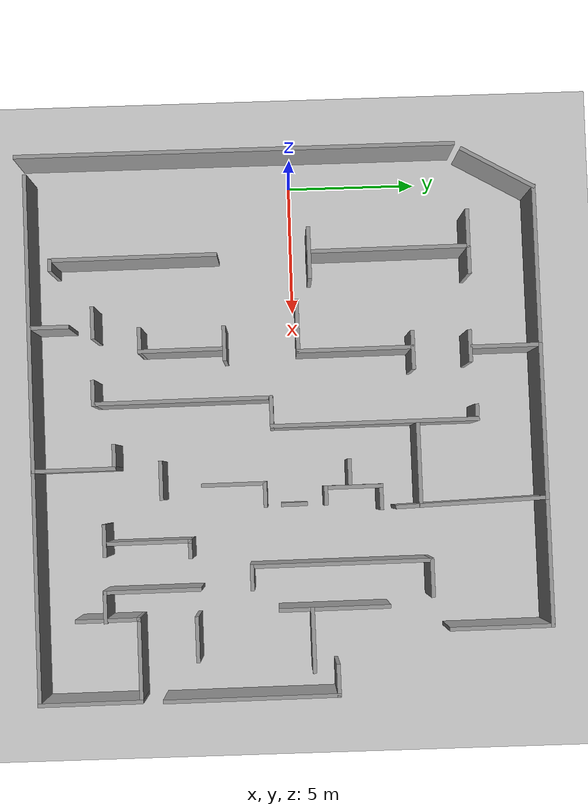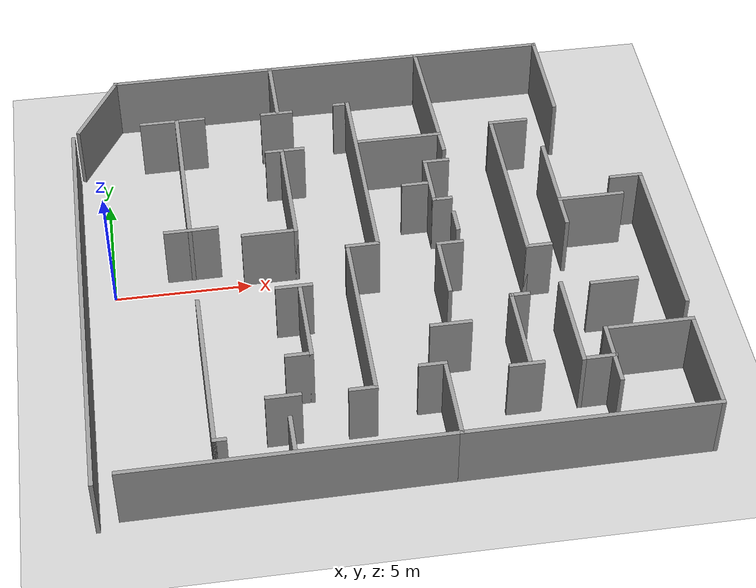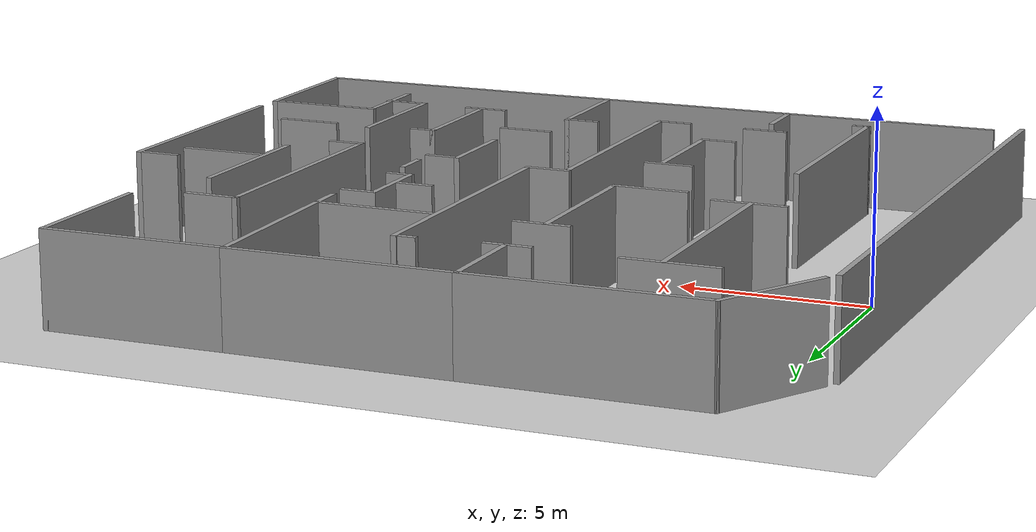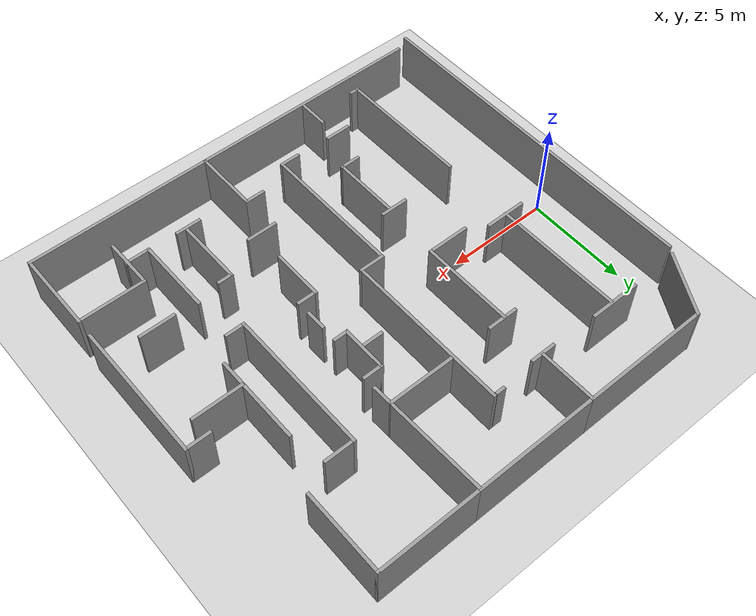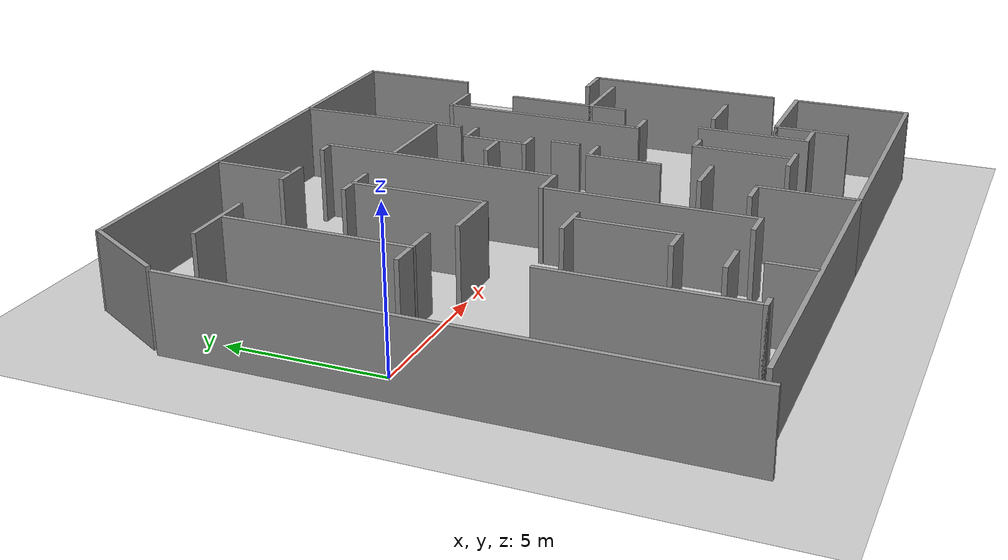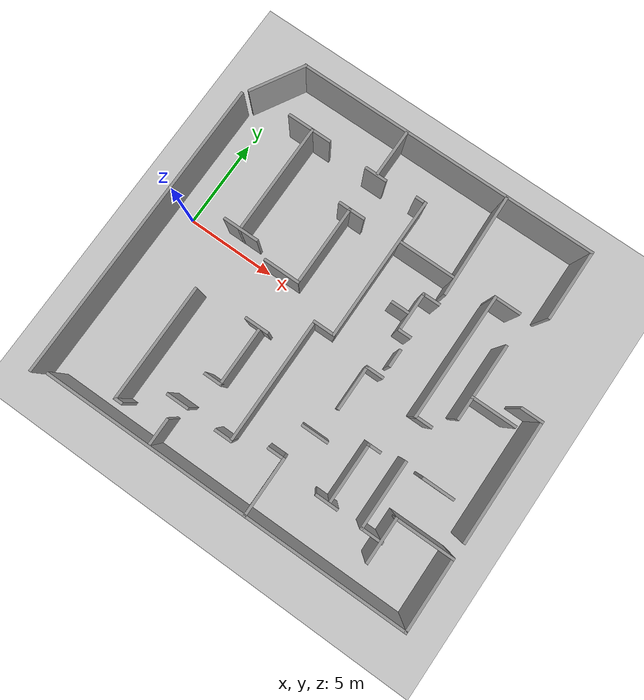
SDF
<sdf version="1.6">
 <world name="default">
  <light name="sun" type="directional">
   <pose>0 0 10 0 -0 0</pose>
   <diffuse>0.8 0.8 0.8 1</diffuse>
   <specular>0.2 0.2 0.2 1</specular>
   <attenuation>
    <range>1000</range>
    <constant>0.9</constant>
    <linear>0.01</linear>
    <quadratic>0.001</quadratic>
   </attenuation>
   <direction>-0.5 0.1 -0.9</direction>
  </light>
  <model name="ground_plane">
   <static>1</static>
   <link name="link">
    <collision name="collision">
     <geometry><plane><normal>0 0 1</normal><size>100 100</size></plane></geometry>
     <surface><friction><ode><mu>100</mu><mu2>50</mu2></ode></friction></surface>
    </collision>
    <visual name="visual">
     <cast_shadows>0</cast_shadows>
     <geometry><plane><normal>0 0 1</normal><size>100 100</size></plane></geometry>
     <material>
      <script><uri>file://media/materials/scripts/gazebo.material</uri><name>Gazebo/Grey</name></script>
     </material>
    </visual>
   </link>
  </model>
  <gravity>0 0 -9.8</gravity>
  <magnetic_field>6e-06 2.3e-05 -4.2e-05</magnetic_field>
  <atmosphere type="adiabatic"/>
  <physics name="default_physics" default="0" type="ode">
   <max_step_size>0.001</max_step_size>
   <real_time_factor>1</real_time_factor>
   <real_time_update_rate>1000</real_time_update_rate>
  </physics>
  <scene><ambient>0.4 0.4 0.4 1</ambient><background>0.7 0.7 0.7 1</background><shadows>1</shadows></scene>
  <audio><device>default</device></audio>
  <spherical_coordinates>
   <surface_model>EARTH_WGS84</surface_model>
   <latitude_deg>0</latitude_deg>
   <longitude_deg>0</longitude_deg>
   <elevation>0</elevation>
   <heading_deg>0</heading_deg>
  </spherical_coordinates>
  <model name="darpa_maze_real">
   <link name="Wall_145">
    <pose>-4.94279 1.78278 0 0 -0 1.5708</pose>
    <visual name="Wall_145_Visual">
     <pose>0 0 1.25 0 -0 0</pose>
     <geometry><box><size>3.25 0.15 2.5</size></box></geometry>
     <material>
      <script><uri>file://media/materials/scripts/gazebo.material</uri><name>Gazebo/Grey</name></script>
      <ambient>1 1 1 1</ambient>
     </material>
     <meta><layer>0</layer></meta>
    </visual>
    <collision name="Wall_145_Collision">
     <pose>0 0 1.25 0 -0 0</pose>
     <geometry><box><size>3.25 0.15 2.5</size></box></geometry>
     <surface>
      <friction>
       <ode><mu>1</mu><mu2>1</mu2><fdir1>0 0 0</fdir1><slip1>0</slip1><slip2>0</slip2></ode>
       <torsional>
        <coefficient>1</coefficient>
        <patch_radius>0</patch_radius>
        <surface_radius>0</surface_radius>
        <use_patch_radius>1</use_patch_radius>
        <ode><slip>0</slip></ode>
       </torsional>
      </friction>
      <bounce><restitution_coefficient>0</restitution_coefficient><threshold>1e+06</threshold></bounce>
      <contact>
       <collide_without_contact>0</collide_without_contact>
       <collide_without_contact_bitmask>1</collide_without_contact_bitmask>
       <collide_bitmask>1</collide_bitmask>
       <ode>
        <soft_cfm>0</soft_cfm>
        <soft_erp>0.2</soft_erp>
        <kp>1e+13</kp>
        <kd>1</kd>
        <max_vel>0.01</max_vel>
        <min_depth>0</min_depth>
       </ode>
       <bullet>
        <split_impulse>1</split_impulse>
        <split_impulse_penetration_threshold>-0.01</split_impulse_penetration_threshold>
        <soft_cfm>0</soft_cfm>
        <soft_erp>0.2</soft_erp>
        <kp>1e+13</kp>
        <kd>1</kd>
       </bullet>
      </contact>
     </surface>
    </collision>
   </link>
   <link name="Wall_148">
    <pose>-9.75516 0.277941 0 0 -0 1.5708</pose>
    <visual name="Wall_148_Visual">
     <pose>0 0 1.25 0 -0 0</pose>
     <geometry><box><size>6 0.15 2.5</size></box></geometry>
     <material>
      <script><uri>file://media/materials/scripts/gazebo.material</uri><name>Gazebo/Grey</name></script>
      <ambient>1 1 1 1</ambient>
     </material>
     <meta><layer>0</layer></meta>
    </visual>
    <collision name="Wall_148_Collision">
     <pose>0 0 1.25 0 -0 0</pose>
     <geometry><box><size>6 0.15 2.5</size></box></geometry>
     <surface>
      <friction>
       <ode><mu>1</mu><mu2>1</mu2><fdir1>0 0 0</fdir1><slip1>0</slip1><slip2>0</slip2></ode>
       <torsional>
        <coefficient>1</coefficient>
        <patch_radius>0</patch_radius>
        <surface_radius>0</surface_radius>
        <use_patch_radius>1</use_patch_radius>
        <ode><slip>0</slip></ode>
       </torsional>
      </friction>
      <bounce><restitution_coefficient>0</restitution_coefficient><threshold>1e+06</threshold></bounce>
      <contact>
       <collide_without_contact>0</collide_without_contact>
       <collide_without_contact_bitmask>1</collide_without_contact_bitmask>
       <collide_bitmask>1</collide_bitmask>
       <ode>
        <soft_cfm>0</soft_cfm>
        <soft_erp>0.2</soft_erp>
        <kp>1e+13</kp>
        <kd>1</kd>
        <max_vel>0.01</max_vel>
        <min_depth>0</min_depth>
       </ode>
       <bullet>
        <split_impulse>1</split_impulse>
        <split_impulse_penetration_threshold>-0.01</split_impulse_penetration_threshold>
        <soft_cfm>0</soft_cfm>
        <soft_erp>0.2</soft_erp>
        <kp>1e+13</kp>
        <kd>1</kd>
       </bullet>
      </contact>
     </surface>
    </collision>
   </link>
   <link name="Wall_154">
    <pose>-6.85816 3.28111 0 0 0 -3.11462</pose>
    <inertial>
     <inertia><ixx>0</ixx><ixy>0</ixy><ixz>0</ixz><iyy>0</iyy><iyz>0</iyz><izz>0</izz></inertia>
     <mass>0</mass>
    </inertial>
    <visual name="Wall_154_Visual">
     <pose>0 0 1.25 0 -0 0</pose>
     <geometry><box><size>5.75605 0.15 2.5</size></box></geometry>
     <material>
      <script><uri>file://media/materials/scripts/gazebo.material</uri><name>Gazebo/Grey</name></script>
      <ambient>1 1 1 1</ambient>
     </material>
     <meta><layer>0</layer></meta>
    </visual>
    <collision name="Wall_154_Collision">
     <pose>0 0 1.25 0 -0 0</pose>
     <geometry><box><size>5.75605 0.15 2.5</size></box></geometry>
     <surface>
      <friction>
       <ode><mu>1</mu><mu2>1</mu2><fdir1>0 0 0</fdir1><slip1>0</slip1><slip2>0</slip2></ode>
       <torsional>
        <coefficient>1</coefficient>
        <patch_radius>0</patch_radius>
        <surface_radius>0</surface_radius>
        <use_patch_radius>1</use_patch_radius>
        <ode><slip>0</slip></ode>
       </torsional>
      </friction>
      <bounce><restitution_coefficient>0</restitution_coefficient><threshold>1e+06</threshold></bounce>
      <contact>
       <collide_without_contact>0</collide_without_contact>
       <collide_without_contact_bitmask>1</collide_without_contact_bitmask>
       <collide_bitmask>1</collide_bitmask>
       <ode>
        <soft_cfm>0</soft_cfm>
        <soft_erp>0.2</soft_erp>
        <kp>1e+13</kp>
        <kd>1</kd>
        <max_vel>0.01</max_vel>
        <min_depth>0</min_depth>
       </ode>
       <bullet>
        <split_impulse>1</split_impulse>
        <split_impulse_penetration_threshold>-0.01</split_impulse_penetration_threshold>
        <soft_cfm>0</soft_cfm>
        <soft_erp>0.2</soft_erp>
        <kp>1e+13</kp>
        <kd>1</kd>
       </bullet>
      </contact>
     </surface>
    </collision>
   </link>
   <link name="Wall_156">
    <pose>9.78261 -4.18195 0 0 -0 1.5708</pose>
    <visual name="Wall_156_Visual">
     <pose>0 0 1.25 0 -0 0</pose>
     <geometry><box><size>11.5 0.15 2.5</size></box></geometry>
     <material>
      <script><uri>file://media/materials/scripts/gazebo.material</uri><name>Gazebo/Grey</name></script>
      <ambient>1 1 1 1</ambient>
     </material>
     <meta><layer>0</layer></meta>
    </visual>
    <collision name="Wall_156_Collision">
     <pose>0 0 1.25 0 -0 0</pose>
     <geometry><box><size>11.5 0.15 2.5</size></box></geometry>
     <surface>
      <friction>
       <ode><mu>1</mu><mu2>1</mu2><fdir1>0 0 0</fdir1><slip1>0</slip1><slip2>0</slip2></ode>
       <torsional>
        <coefficient>1</coefficient>
        <patch_radius>0</patch_radius>
        <surface_radius>0</surface_radius>
        <use_patch_radius>1</use_patch_radius>
        <ode><slip>0</slip></ode>
       </torsional>
      </friction>
      <bounce><restitution_coefficient>0</restitution_coefficient><threshold>1e+06</threshold></bounce>
      <contact>
       <collide_without_contact>0</collide_without_contact>
       <collide_without_contact_bitmask>1</collide_without_contact_bitmask>
       <collide_bitmask>1</collide_bitmask>
       <ode>
        <soft_cfm>0</soft_cfm>
        <soft_erp>0.2</soft_erp>
        <kp>1e+13</kp>
        <kd>1</kd>
        <max_vel>0.01</max_vel>
        <min_depth>0</min_depth>
       </ode>
       <bullet>
        <split_impulse>1</split_impulse>
        <split_impulse_penetration_threshold>-0.01</split_impulse_penetration_threshold>
        <soft_cfm>0</soft_cfm>
        <soft_erp>0.2</soft_erp>
        <kp>1e+13</kp>
        <kd>1</kd>
       </bullet>
      </contact>
     </surface>
    </collision>
   </link>
   <link name="Wall_157">
    <pose>8.23261 1.49305 0 0 -0 3.14159</pose>
    <visual name="Wall_157_Visual">
     <pose>0 0 1.25 0 -0 0</pose>
     <geometry><box><size>3.25 0.15 2.5</size></box></geometry>
     <material>
      <script><uri>file://media/materials/scripts/gazebo.material</uri><name>Gazebo/Grey</name></script>
      <ambient>1 1 1 1</ambient>
     </material>
     <meta><layer>0</layer></meta>
    </visual>
    <collision name="Wall_157_Collision">
     <pose>0 0 1.25 0 -0 0</pose>
     <geometry><box><size>3.25 0.15 2.5</size></box></geometry>
     <surface>
      <friction>
       <ode><mu>1</mu><mu2>1</mu2><fdir1>0 0 0</fdir1><slip1>0</slip1><slip2>0</slip2></ode>
       <torsional>
        <coefficient>1</coefficient>
        <patch_radius>0</patch_radius>
        <surface_radius>0</surface_radius>
        <use_patch_radius>1</use_patch_radius>
        <ode><slip>0</slip></ode>
       </torsional>
      </friction>
      <bounce><restitution_coefficient>0</restitution_coefficient><threshold>1e+06</threshold></bounce>
      <contact>
       <collide_without_contact>0</collide_without_contact>
       <collide_without_contact_bitmask>1</collide_without_contact_bitmask>
       <collide_bitmask>1</collide_bitmask>
       <ode>
        <soft_cfm>0</soft_cfm>
        <soft_erp>0.2</soft_erp>
        <kp>1e+13</kp>
        <kd>1</kd>
        <max_vel>0.01</max_vel>
        <min_depth>0</min_depth>
       </ode>
       <bullet>
        <split_impulse>1</split_impulse>
        <split_impulse_penetration_threshold>-0.01</split_impulse_penetration_threshold>
        <soft_cfm>0</soft_cfm>
        <soft_erp>0.2</soft_erp>
        <kp>1e+13</kp>
        <kd>1</kd>
       </bullet>
      </contact>
     </surface>
    </collision>
   </link>
   <link name="Wall_158">
    <pose>6.68261 1.06805 0 0 0 -1.5708</pose>
    <visual name="Wall_158_Visual">
     <pose>0 0 1.25 0 -0 0</pose>
     <geometry><box><size>1 0.15 2.5</size></box></geometry>
     <material>
      <script><uri>file://media/materials/scripts/gazebo.material</uri><name>Gazebo/Grey</name></script>
      <ambient>1 1 1 1</ambient>
     </material>
     <meta><layer>0</layer></meta>
    </visual>
    <collision name="Wall_158_Collision">
     <pose>0 0 1.25 0 -0 0</pose>
     <geometry><box><size>1 0.15 2.5</size></box></geometry>
     <surface>
      <friction>
       <ode><mu>1</mu><mu2>1</mu2><fdir1>0 0 0</fdir1><slip1>0</slip1><slip2>0</slip2></ode>
       <torsional>
        <coefficient>1</coefficient>
        <patch_radius>0</patch_radius>
        <surface_radius>0</surface_radius>
        <use_patch_radius>1</use_patch_radius>
        <ode><slip>0</slip></ode>
       </torsional>
      </friction>
      <bounce><restitution_coefficient>0</restitution_coefficient><threshold>1e+06</threshold></bounce>
      <contact>
       <collide_without_contact>0</collide_without_contact>
       <collide_without_contact_bitmask>1</collide_without_contact_bitmask>
       <collide_bitmask>1</collide_bitmask>
       <ode>
        <soft_cfm>0</soft_cfm>
        <soft_erp>0.2</soft_erp>
        <kp>1e+13</kp>
        <kd>1</kd>
        <max_vel>0.01</max_vel>
        <min_depth>0</min_depth>
       </ode>
       <bullet>
        <split_impulse>1</split_impulse>
        <split_impulse_penetration_threshold>-0.01</split_impulse_penetration_threshold>
        <soft_cfm>0</soft_cfm>
        <soft_erp>0.2</soft_erp>
        <kp>1e+13</kp>
        <kd>1</kd>
       </bullet>
      </contact>
     </surface>
    </collision>
   </link>
   <link name="Wall_160">
    <pose>4.9219 2.01613 0 0 -0 1.5708</pose>
    <visual name="Wall_160_Visual">
     <pose>0 0 1.25 0 -0 0</pose>
     <geometry><box><size>1.5 0.15 2.5</size></box></geometry>
     <material>
      <script><uri>file://media/materials/scripts/gazebo.material</uri><name>Gazebo/Grey</name></script>
      <ambient>1 1 1 1</ambient>
     </material>
     <meta><layer>0</layer></meta>
    </visual>
    <collision name="Wall_160_Collision">
     <pose>0 0 1.25 0 -0 0</pose>
     <geometry><box><size>1.5 0.15 2.5</size></box></geometry>
     <surface>
      <friction>
       <ode><mu>1</mu><mu2>1</mu2><fdir1>0 0 0</fdir1><slip1>0</slip1><slip2>0</slip2></ode>
       <torsional>
        <coefficient>1</coefficient>
        <patch_radius>0</patch_radius>
        <surface_radius>0</surface_radius>
        <use_patch_radius>1</use_patch_radius>
        <ode><slip>0</slip></ode>
       </torsional>
      </friction>
      <bounce><restitution_coefficient>0</restitution_coefficient><threshold>1e+06</threshold></bounce>
      <contact>
       <collide_without_contact>0</collide_without_contact>
       <collide_without_contact_bitmask>1</collide_without_contact_bitmask>
       <collide_bitmask>1</collide_bitmask>
       <ode>
        <soft_cfm>0</soft_cfm>
        <soft_erp>0.2</soft_erp>
        <kp>1e+13</kp>
        <kd>1</kd>
        <max_vel>0.01</max_vel>
        <min_depth>0</min_depth>
       </ode>
       <bullet>
        <split_impulse>1</split_impulse>
        <split_impulse_penetration_threshold>-0.01</split_impulse_penetration_threshold>
        <soft_cfm>0</soft_cfm>
        <soft_erp>0.2</soft_erp>
        <kp>1e+13</kp>
        <kd>1</kd>
       </bullet>
      </contact>
     </surface>
    </collision>
   </link>
   <link name="Wall_162">
    <pose>2.14718 2.26404 0 0 -0 3.14159</pose>
    <visual name="Wall_162_Visual">
     <pose>0 0 1.25 0 -0 0</pose>
     <geometry><box><size>2.5 0.15 2.5</size></box></geometry>
     <material>
      <script><uri>file://media/materials/scripts/gazebo.material</uri><name>Gazebo/Grey</name></script>
      <ambient>1 1 1 1</ambient>
     </material>
     <meta><layer>0</layer></meta>
    </visual>
    <collision name="Wall_162_Collision">
     <pose>0 0 1.25 0 -0 0</pose>
     <geometry><box><size>2.5 0.15 2.5</size></box></geometry>
     <surface>
      <friction>
       <ode><mu>1</mu><mu2>1</mu2><fdir1>0 0 0</fdir1><slip1>0</slip1><slip2>0</slip2></ode>
       <torsional>
        <coefficient>1</coefficient>
        <patch_radius>0</patch_radius>
        <surface_radius>0</surface_radius>
        <use_patch_radius>1</use_patch_radius>
        <ode><slip>0</slip></ode>
       </torsional>
      </friction>
      <bounce><restitution_coefficient>0</restitution_coefficient><threshold>1e+06</threshold></bounce>
      <contact>
       <collide_without_contact>0</collide_without_contact>
       <collide_without_contact_bitmask>1</collide_without_contact_bitmask>
       <collide_bitmask>1</collide_bitmask>
       <ode>
        <soft_cfm>0</soft_cfm>
        <soft_erp>0.2</soft_erp>
        <kp>1e+13</kp>
        <kd>1</kd>
        <max_vel>0.01</max_vel>
        <min_depth>0</min_depth>
       </ode>
       <bullet>
        <split_impulse>1</split_impulse>
        <split_impulse_penetration_threshold>-0.01</split_impulse_penetration_threshold>
        <soft_cfm>0</soft_cfm>
        <soft_erp>0.2</soft_erp>
        <kp>1e+13</kp>
        <kd>1</kd>
       </bullet>
      </contact>
     </surface>
    </collision>
   </link>
   <link name="Wall_163">
    <pose>0.972182 2.68905 0 0 -0 1.5708</pose>
    <visual name="Wall_163_Visual">
     <pose>0 0 1.25 0 -0 0</pose>
     <geometry><box><size>1 0.15 2.5</size></box></geometry>
     <material>
      <script><uri>file://media/materials/scripts/gazebo.material</uri><name>Gazebo/Grey</name></script>
      <ambient>1 1 1 1</ambient>
     </material>
     <meta><layer>0</layer></meta>
    </visual>
    <collision name="Wall_163_Collision">
     <pose>0 0 1.25 0 -0 0</pose>
     <geometry><box><size>1 0.15 2.5</size></box></geometry>
     <surface>
      <friction>
       <ode><mu>1</mu><mu2>1</mu2><fdir1>0 0 0</fdir1><slip1>0</slip1><slip2>0</slip2></ode>
       <torsional>
        <coefficient>1</coefficient>
        <patch_radius>0</patch_radius>
        <surface_radius>0</surface_radius>
        <use_patch_radius>1</use_patch_radius>
        <ode><slip>0</slip></ode>
       </torsional>
      </friction>
      <bounce><restitution_coefficient>0</restitution_coefficient><threshold>1e+06</threshold></bounce>
      <contact>
       <collide_without_contact>0</collide_without_contact>
       <collide_without_contact_bitmask>1</collide_without_contact_bitmask>
       <collide_bitmask>1</collide_bitmask>
       <ode>
        <soft_cfm>0</soft_cfm>
        <soft_erp>0.2</soft_erp>
        <kp>1e+13</kp>
        <kd>1</kd>
        <max_vel>0.01</max_vel>
        <min_depth>0</min_depth>
       </ode>
       <bullet>
        <split_impulse>1</split_impulse>
        <split_impulse_penetration_threshold>-0.01</split_impulse_penetration_threshold>
        <soft_cfm>0</soft_cfm>
        <soft_erp>0.2</soft_erp>
        <kp>1e+13</kp>
        <kd>1</kd>
       </bullet>
      </contact>
     </surface>
    </collision>
   </link>
   <link name="Wall_165">
    <pose>-3.44589 2.94655 0 0 0 -1.5708</pose>
    <visual name="Wall_165_Visual">
     <pose>0 0 1.25 0 -0 0</pose>
     <geometry><box><size>1 0.15 2.5</size></box></geometry>
     <material>
      <script><uri>file://media/materials/scripts/gazebo.material</uri><name>Gazebo/Grey</name></script>
      <ambient>1 1 1 1</ambient>
     </material>
     <meta><layer>0</layer></meta>
    </visual>
    <collision name="Wall_165_Collision">
     <pose>0 0 1.25 0 -0 0</pose>
     <geometry><box><size>1 0.15 2.5</size></box></geometry>
     <surface>
      <friction>
       <ode><mu>1</mu><mu2>1</mu2><fdir1>0 0 0</fdir1><slip1>0</slip1><slip2>0</slip2></ode>
       <torsional>
        <coefficient>1</coefficient>
        <patch_radius>0</patch_radius>
        <surface_radius>0</surface_radius>
        <use_patch_radius>1</use_patch_radius>
        <ode><slip>0</slip></ode>
       </torsional>
      </friction>
      <bounce><restitution_coefficient>0</restitution_coefficient><threshold>1e+06</threshold></bounce>
      <contact>
       <collide_without_contact>0</collide_without_contact>
       <collide_without_contact_bitmask>1</collide_without_contact_bitmask>
       <collide_bitmask>1</collide_bitmask>
       <ode>
        <soft_cfm>0</soft_cfm>
        <soft_erp>0.2</soft_erp>
        <kp>1e+13</kp>
        <kd>1</kd>
        <max_vel>0.01</max_vel>
        <min_depth>0</min_depth>
       </ode>
       <bullet>
        <split_impulse>1</split_impulse>
        <split_impulse_penetration_threshold>-0.01</split_impulse_penetration_threshold>
        <soft_cfm>0</soft_cfm>
        <soft_erp>0.2</soft_erp>
        <kp>1e+13</kp>
        <kd>1</kd>
       </bullet>
      </contact>
     </surface>
    </collision>
   </link>
   <link name="Wall_166">
    <pose>-2.39589 2.52155 0 0 -0 0</pose>
    <visual name="Wall_166_Visual">
     <pose>0 0 1.25 0 -0 0</pose>
     <geometry><box><size>2.25 0.15 2.5</size></box></geometry>
     <material>
      <script><uri>file://media/materials/scripts/gazebo.material</uri><name>Gazebo/Grey</name></script>
      <ambient>1 1 1 1</ambient>
     </material>
     <meta><layer>0</layer></meta>
    </visual>
    <collision name="Wall_166_Collision">
     <pose>0 0 1.25 0 -0 0</pose>
     <geometry><box><size>2.25 0.15 2.5</size></box></geometry>
     <surface>
      <friction>
       <ode><mu>1</mu><mu2>1</mu2><fdir1>0 0 0</fdir1><slip1>0</slip1><slip2>0</slip2></ode>
       <torsional>
        <coefficient>1</coefficient>
        <patch_radius>0</patch_radius>
        <surface_radius>0</surface_radius>
        <use_patch_radius>1</use_patch_radius>
        <ode><slip>0</slip></ode>
       </torsional>
      </friction>
      <bounce><restitution_coefficient>0</restitution_coefficient><threshold>1e+06</threshold></bounce>
      <contact>
       <collide_without_contact>0</collide_without_contact>
       <collide_without_contact_bitmask>1</collide_without_contact_bitmask>
       <collide_bitmask>1</collide_bitmask>
       <ode>
        <soft_cfm>0</soft_cfm>
        <soft_erp>0.2</soft_erp>
        <kp>1e+13</kp>
        <kd>1</kd>
        <max_vel>0.01</max_vel>
        <min_depth>0</min_depth>
       </ode>
       <bullet>
        <split_impulse>1</split_impulse>
        <split_impulse_penetration_threshold>-0.01</split_impulse_penetration_threshold>
        <soft_cfm>0</soft_cfm>
        <soft_erp>0.2</soft_erp>
        <kp>1e+13</kp>
        <kd>1</kd>
       </bullet>
      </contact>
     </surface>
    </collision>
   </link>
   <link name="Wall_167">
    <pose>-1.34589 2.82155 0 0 -0 1.5708</pose>
    <visual name="Wall_167_Visual">
     <pose>0 0 1.25 0 -0 0</pose>
     <geometry><box><size>0.75 0.15 2.5</size></box></geometry>
     <material>
      <script><uri>file://media/materials/scripts/gazebo.material</uri><name>Gazebo/Grey</name></script>
      <ambient>1 1 1 1</ambient>
     </material>
     <meta><layer>0</layer></meta>
    </visual>
    <collision name="Wall_167_Collision">
     <pose>0 0 1.25 0 -0 0</pose>
     <geometry><box><size>0.75 0.15 2.5</size></box></geometry>
     <surface>
      <friction>
       <ode><mu>1</mu><mu2>1</mu2><fdir1>0 0 0</fdir1><slip1>0</slip1><slip2>0</slip2></ode>
       <torsional>
        <coefficient>1</coefficient>
        <patch_radius>0</patch_radius>
        <surface_radius>0</surface_radius>
        <use_patch_radius>1</use_patch_radius>
        <ode><slip>0</slip></ode>
       </torsional>
      </friction>
      <bounce><restitution_coefficient>0</restitution_coefficient><threshold>1e+06</threshold></bounce>
      <contact>
       <collide_without_contact>0</collide_without_contact>
       <collide_without_contact_bitmask>1</collide_without_contact_bitmask>
       <collide_bitmask>1</collide_bitmask>
       <ode>
        <soft_cfm>0</soft_cfm>
        <soft_erp>0.2</soft_erp>
        <kp>1e+13</kp>
        <kd>1</kd>
        <max_vel>0.01</max_vel>
        <min_depth>0</min_depth>
       </ode>
       <bullet>
        <split_impulse>1</split_impulse>
        <split_impulse_penetration_threshold>-0.01</split_impulse_penetration_threshold>
        <soft_cfm>0</soft_cfm>
        <soft_erp>0.2</soft_erp>
        <kp>1e+13</kp>
        <kd>1</kd>
       </bullet>
      </contact>
     </surface>
    </collision>
   </link>
   <link name="Wall_169">
    <pose>-2.27686 1.95071 0 0 -0 1.5708</pose>
    <visual name="Wall_169_Visual">
     <pose>0 0 1.25 0 -0 0</pose>
     <geometry><box><size>1 0.15 2.5</size></box></geometry>
     <material>
      <script><uri>file://media/materials/scripts/gazebo.material</uri><name>Gazebo/Grey</name></script>
      <ambient>1 1 1 1</ambient>
     </material>
     <meta><layer>0</layer></meta>
    </visual>
    <collision name="Wall_169_Collision">
     <pose>0 0 1.25 0 -0 0</pose>
     <geometry><box><size>1 0.15 2.5</size></box></geometry>
     <surface>
      <friction>
       <ode><mu>1</mu><mu2>1</mu2><fdir1>0 0 0</fdir1><slip1>0</slip1><slip2>0</slip2></ode>
       <torsional>
        <coefficient>1</coefficient>
        <patch_radius>0</patch_radius>
        <surface_radius>0</surface_radius>
        <use_patch_radius>1</use_patch_radius>
        <ode><slip>0</slip></ode>
       </torsional>
      </friction>
      <bounce><restitution_coefficient>0</restitution_coefficient><threshold>1e+06</threshold></bounce>
      <contact>
       <collide_without_contact>0</collide_without_contact>
       <collide_without_contact_bitmask>1</collide_without_contact_bitmask>
       <collide_bitmask>1</collide_bitmask>
       <ode>
        <soft_cfm>0</soft_cfm>
        <soft_erp>0.2</soft_erp>
        <kp>1e+13</kp>
        <kd>1</kd>
        <max_vel>0.01</max_vel>
        <min_depth>0</min_depth>
       </ode>
       <bullet>
        <split_impulse>1</split_impulse>
        <split_impulse_penetration_threshold>-0.01</split_impulse_penetration_threshold>
        <soft_cfm>0</soft_cfm>
        <soft_erp>0.2</soft_erp>
        <kp>1e+13</kp>
        <kd>1</kd>
       </bullet>
      </contact>
     </surface>
    </collision>
   </link>
   <link name="Wall_171">
    <pose>3.8951 4.65021 0 0 0 -1.5708</pose>
    <visual name="Wall_171_Visual">
     <pose>0 0 1.25 0 -0 0</pose>
     <geometry><box><size>0.75 0.15 2.5</size></box></geometry>
     <material>
      <script><uri>file://media/materials/scripts/gazebo.material</uri><name>Gazebo/Grey</name></script>
      <ambient>1 1 1 1</ambient>
     </material>
     <meta><layer>0</layer></meta>
    </visual>
    <collision name="Wall_171_Collision">
     <pose>0 0 1.25 0 -0 0</pose>
     <geometry><box><size>0.75 0.15 2.5</size></box></geometry>
     <surface>
      <friction>
       <ode><mu>1</mu><mu2>1</mu2><fdir1>0 0 0</fdir1><slip1>0</slip1><slip2>0</slip2></ode>
       <torsional>
        <coefficient>1</coefficient>
        <patch_radius>0</patch_radius>
        <surface_radius>0</surface_radius>
        <use_patch_radius>1</use_patch_radius>
        <ode><slip>0</slip></ode>
       </torsional>
      </friction>
      <bounce><restitution_coefficient>0</restitution_coefficient><threshold>1e+06</threshold></bounce>
      <contact>
       <collide_without_contact>0</collide_without_contact>
       <collide_without_contact_bitmask>1</collide_without_contact_bitmask>
       <collide_bitmask>1</collide_bitmask>
       <ode>
        <soft_cfm>0</soft_cfm>
        <soft_erp>0.2</soft_erp>
        <kp>1e+13</kp>
        <kd>1</kd>
        <max_vel>0.01</max_vel>
        <min_depth>0</min_depth>
       </ode>
       <bullet>
        <split_impulse>1</split_impulse>
        <split_impulse_penetration_threshold>-0.01</split_impulse_penetration_threshold>
        <soft_cfm>0</soft_cfm>
        <soft_erp>0.2</soft_erp>
        <kp>1e+13</kp>
        <kd>1</kd>
       </bullet>
      </contact>
     </surface>
    </collision>
   </link>
   <link name="Wall_174">
    <pose>7.14993 4.22658 0 0 -0 1.5708</pose>
    <visual name="Wall_174_Visual">
     <pose>0 0 1.25 0 -0 0</pose>
     <geometry><box><size>1.25 0.15 2.5</size></box></geometry>
     <material>
      <script><uri>file://media/materials/scripts/gazebo.material</uri><name>Gazebo/Grey</name></script>
      <ambient>1 1 1 1</ambient>
     </material>
     <meta><layer>0</layer></meta>
    </visual>
    <collision name="Wall_174_Collision">
     <pose>0 0 1.25 0 -0 0</pose>
     <geometry><box><size>1.25 0.15 2.5</size></box></geometry>
     <surface>
      <friction>
       <ode><mu>1</mu><mu2>1</mu2><fdir1>0 0 0</fdir1><slip1>0</slip1><slip2>0</slip2></ode>
       <torsional>
        <coefficient>1</coefficient>
        <patch_radius>0</patch_radius>
        <surface_radius>0</surface_radius>
        <use_patch_radius>1</use_patch_radius>
        <ode><slip>0</slip></ode>
       </torsional>
      </friction>
      <bounce><restitution_coefficient>0</restitution_coefficient><threshold>1e+06</threshold></bounce>
      <contact>
       <collide_without_contact>0</collide_without_contact>
       <collide_without_contact_bitmask>1</collide_without_contact_bitmask>
       <collide_bitmask>1</collide_bitmask>
       <ode>
        <soft_cfm>0</soft_cfm>
        <soft_erp>0.2</soft_erp>
        <kp>1e+13</kp>
        <kd>1</kd>
        <max_vel>0.01</max_vel>
        <min_depth>0</min_depth>
       </ode>
       <bullet>
        <split_impulse>1</split_impulse>
        <split_impulse_penetration_threshold>-0.01</split_impulse_penetration_threshold>
        <soft_cfm>0</soft_cfm>
        <soft_erp>0.2</soft_erp>
        <kp>1e+13</kp>
        <kd>1</kd>
       </bullet>
      </contact>
     </surface>
    </collision>
   </link>
   <link name="Wall_176">
    <pose>5.4451 4.35021 0 0 -0 0</pose>
    <visual name="Wall_176_Visual">
     <pose>0 0 1.25 0 -0 0</pose>
     <geometry><box><size>3.25 0.15 2.5</size></box></geometry>
     <material>
      <script><uri>file://media/materials/scripts/gazebo.material</uri><name>Gazebo/Grey</name></script>
      <ambient>1 1 1 1</ambient>
     </material>
     <meta><layer>0</layer></meta>
    </visual>
    <collision name="Wall_176_Collision">
     <pose>0 0 1.25 0 -0 0</pose>
     <geometry><box><size>3.25 0.15 2.5</size></box></geometry>
     <surface>
      <friction>
       <ode><mu>1</mu><mu2>1</mu2><fdir1>0 0 0</fdir1><slip1>0</slip1><slip2>0</slip2></ode>
       <torsional>
        <coefficient>1</coefficient>
        <patch_radius>0</patch_radius>
        <surface_radius>0</surface_radius>
        <use_patch_radius>1</use_patch_radius>
        <ode><slip>0</slip></ode>
       </torsional>
      </friction>
      <bounce><restitution_coefficient>0</restitution_coefficient><threshold>1e+06</threshold></bounce>
      <contact>
       <collide_without_contact>0</collide_without_contact>
       <collide_without_contact_bitmask>1</collide_without_contact_bitmask>
       <collide_bitmask>1</collide_bitmask>
       <ode>
        <soft_cfm>0</soft_cfm>
        <soft_erp>0.2</soft_erp>
        <kp>1e+13</kp>
        <kd>1</kd>
        <max_vel>0.01</max_vel>
        <min_depth>0</min_depth>
       </ode>
       <bullet>
        <split_impulse>1</split_impulse>
        <split_impulse_penetration_threshold>-0.01</split_impulse_penetration_threshold>
        <soft_cfm>0</soft_cfm>
        <soft_erp>0.2</soft_erp>
        <kp>1e+13</kp>
        <kd>1</kd>
       </bullet>
      </contact>
     </surface>
    </collision>
   </link>
   <link name="Wall_178">
    <pose>-0.12433 3.10656 0 0 -0 4e-06</pose>
    <visual name="Wall_178_Visual">
     <pose>0 0 1.25 0 -0 0</pose>
     <geometry><box><size>1 0.15 2.5</size></box></geometry>
     <material>
      <script><uri>file://media/materials/scripts/gazebo.material</uri><name>Gazebo/Grey</name></script>
      <ambient>1 1 1 1</ambient>
     </material>
     <meta><layer>0</layer></meta>
    </visual>
    <collision name="Wall_178_Collision">
     <pose>0 0 1.25 0 -0 0</pose>
     <geometry><box><size>1 0.15 2.5</size></box></geometry>
     <surface>
      <friction>
       <ode><mu>1</mu><mu2>1</mu2><fdir1>0 0 0</fdir1><slip1>0</slip1><slip2>0</slip2></ode>
       <torsional>
        <coefficient>1</coefficient>
        <patch_radius>0</patch_radius>
        <surface_radius>0</surface_radius>
        <use_patch_radius>1</use_patch_radius>
        <ode><slip>0</slip></ode>
       </torsional>
      </friction>
      <bounce><restitution_coefficient>0</restitution_coefficient><threshold>1e+06</threshold></bounce>
      <contact>
       <collide_without_contact>0</collide_without_contact>
       <collide_without_contact_bitmask>1</collide_without_contact_bitmask>
       <collide_bitmask>1</collide_bitmask>
       <ode>
        <soft_cfm>0</soft_cfm>
        <soft_erp>0.2</soft_erp>
        <kp>1e+13</kp>
        <kd>1</kd>
        <max_vel>0.01</max_vel>
        <min_depth>0</min_depth>
       </ode>
       <bullet>
        <split_impulse>1</split_impulse>
        <split_impulse_penetration_threshold>-0.01</split_impulse_penetration_threshold>
        <soft_cfm>0</soft_cfm>
        <soft_erp>0.2</soft_erp>
        <kp>1e+13</kp>
        <kd>1</kd>
       </bullet>
      </contact>
     </surface>
    </collision>
   </link>
   <link name="Wall_188">
    <pose>9.78261 5.91805 0 0 -0 1.5708</pose>
    <visual name="Wall_188_Visual">
     <pose>0 0 1.25 0 -0 0</pose>
     <geometry><box><size>9 0.15 2.5</size></box></geometry>
     <material>
      <script><uri>file://media/materials/scripts/gazebo.material</uri><name>Gazebo/Grey</name></script>
      <ambient>1 1 1 1</ambient>
     </material>
     <meta><layer>0</layer></meta>
    </visual>
    <collision name="Wall_188_Collision">
     <pose>0 0 1.25 0 -0 0</pose>
     <geometry><box><size>9 0.15 2.5</size></box></geometry>
     <surface>
      <friction>
       <ode><mu>1</mu><mu2>1</mu2><fdir1>0 0 0</fdir1><slip1>0</slip1><slip2>0</slip2></ode>
       <torsional>
        <coefficient>1</coefficient>
        <patch_radius>0</patch_radius>
        <surface_radius>0</surface_radius>
        <use_patch_radius>1</use_patch_radius>
        <ode><slip>0</slip></ode>
       </torsional>
      </friction>
      <bounce><restitution_coefficient>0</restitution_coefficient><threshold>1e+06</threshold></bounce>
      <contact>
       <collide_without_contact>0</collide_without_contact>
       <collide_without_contact_bitmask>1</collide_without_contact_bitmask>
       <collide_bitmask>1</collide_bitmask>
       <ode>
        <soft_cfm>0</soft_cfm>
        <soft_erp>0.2</soft_erp>
        <kp>1e+13</kp>
        <kd>1</kd>
        <max_vel>0.01</max_vel>
        <min_depth>0</min_depth>
       </ode>
       <bullet>
        <split_impulse>1</split_impulse>
        <split_impulse_penetration_threshold>-0.01</split_impulse_penetration_threshold>
        <soft_cfm>0</soft_cfm>
        <soft_erp>0.2</soft_erp>
        <kp>1e+13</kp>
        <kd>1</kd>
       </bullet>
      </contact>
     </surface>
    </collision>
   </link>
   <link name="Wall_189">
    <pose>7.85761 10.3431 0 0 -0 3.14159</pose>
    <visual name="Wall_189_Visual">
     <pose>0 0 1.25 0 -0 0</pose>
     <geometry><box><size>4 0.15 2.5</size></box></geometry>
     <material>
      <script><uri>file://media/materials/scripts/gazebo.material</uri><name>Gazebo/Grey</name></script>
      <ambient>1 1 1 1</ambient>
     </material>
     <meta><layer>0</layer></meta>
    </visual>
    <collision name="Wall_189_Collision">
     <pose>0 0 1.25 0 -0 0</pose>
     <geometry><box><size>4 0.15 2.5</size></box></geometry>
     <surface>
      <friction>
       <ode><mu>1</mu><mu2>1</mu2><fdir1>0 0 0</fdir1><slip1>0</slip1><slip2>0</slip2></ode>
       <torsional>
        <coefficient>1</coefficient>
        <patch_radius>0</patch_radius>
        <surface_radius>0</surface_radius>
        <use_patch_radius>1</use_patch_radius>
        <ode><slip>0</slip></ode>
       </torsional>
      </friction>
      <bounce><restitution_coefficient>0</restitution_coefficient><threshold>1e+06</threshold></bounce>
      <contact>
       <collide_without_contact>0</collide_without_contact>
       <collide_without_contact_bitmask>1</collide_without_contact_bitmask>
       <collide_bitmask>1</collide_bitmask>
       <ode>
        <soft_cfm>0</soft_cfm>
        <soft_erp>0.2</soft_erp>
        <kp>1e+13</kp>
        <kd>1</kd>
        <max_vel>0.01</max_vel>
        <min_depth>0</min_depth>
       </ode>
       <bullet>
        <split_impulse>1</split_impulse>
        <split_impulse_penetration_threshold>-0.01</split_impulse_penetration_threshold>
        <soft_cfm>0</soft_cfm>
        <soft_erp>0.2</soft_erp>
        <kp>1e+13</kp>
        <kd>1</kd>
       </bullet>
      </contact>
     </surface>
    </collision>
   </link>
   <link name="Wall_192">
    <pose>5.93261 8.79305 0 0 0 -1.5708</pose>
    <visual name="Wall_192_Visual">
     <pose>0 0 1.25 0 -0 0</pose>
     <geometry><box><size>3.25 0.15 2.5</size></box></geometry>
     <material>
      <script><uri>file://media/materials/scripts/gazebo.material</uri><name>Gazebo/Grey</name></script>
      <ambient>1 1 1 1</ambient>
     </material>
     <meta><layer>0</layer></meta>
    </visual>
    <collision name="Wall_192_Collision">
     <pose>0 0 1.25 0 -0 0</pose>
     <geometry><box><size>3.25 0.15 2.5</size></box></geometry>
     <surface>
      <friction>
       <ode><mu>1</mu><mu2>1</mu2><fdir1>0 0 0</fdir1><slip1>0</slip1><slip2>0</slip2></ode>
       <torsional>
        <coefficient>1</coefficient>
        <patch_radius>0</patch_radius>
        <surface_radius>0</surface_radius>
        <use_patch_radius>1</use_patch_radius>
        <ode><slip>0</slip></ode>
       </torsional>
      </friction>
      <bounce><restitution_coefficient>0</restitution_coefficient><threshold>1e+06</threshold></bounce>
      <contact>
       <collide_without_contact>0</collide_without_contact>
       <collide_without_contact_bitmask>1</collide_without_contact_bitmask>
       <collide_bitmask>1</collide_bitmask>
       <ode>
        <soft_cfm>0</soft_cfm>
        <soft_erp>0.2</soft_erp>
        <kp>1e+13</kp>
        <kd>1</kd>
        <max_vel>0.01</max_vel>
        <min_depth>0</min_depth>
       </ode>
       <bullet>
        <split_impulse>1</split_impulse>
        <split_impulse_penetration_threshold>-0.01</split_impulse_penetration_threshold>
        <soft_cfm>0</soft_cfm>
        <soft_erp>0.2</soft_erp>
        <kp>1e+13</kp>
        <kd>1</kd>
       </bullet>
      </contact>
     </surface>
    </collision>
   </link>
   <link name="Wall_193">
    <pose>7.10761 7.24305 0 0 -0 0</pose>
    <visual name="Wall_193_Visual">
     <pose>0 0 1.25 0 -0 0</pose>
     <geometry><box><size>2.5 0.15 2.5</size></box></geometry>
     <material>
      <script><uri>file://media/materials/scripts/gazebo.material</uri><name>Gazebo/Grey</name></script>
      <ambient>1 1 1 1</ambient>
     </material>
     <meta><layer>0</layer></meta>
    </visual>
    <collision name="Wall_193_Collision">
     <pose>0 0 1.25 0 -0 0</pose>
     <geometry><box><size>2.5 0.15 2.5</size></box></geometry>
     <surface>
      <friction>
       <ode><mu>1</mu><mu2>1</mu2><fdir1>0 0 0</fdir1><slip1>0</slip1><slip2>0</slip2></ode>
       <torsional>
        <coefficient>1</coefficient>
        <patch_radius>0</patch_radius>
        <surface_radius>0</surface_radius>
        <use_patch_radius>1</use_patch_radius>
        <ode><slip>0</slip></ode>
       </torsional>
      </friction>
      <bounce><restitution_coefficient>0</restitution_coefficient><threshold>1e+06</threshold></bounce>
      <contact>
       <collide_without_contact>0</collide_without_contact>
       <collide_without_contact_bitmask>1</collide_without_contact_bitmask>
       <collide_bitmask>1</collide_bitmask>
       <ode>
        <soft_cfm>0</soft_cfm>
        <soft_erp>0.2</soft_erp>
        <kp>1e+13</kp>
        <kd>1</kd>
        <max_vel>0.01</max_vel>
        <min_depth>0</min_depth>
       </ode>
       <bullet>
        <split_impulse>1</split_impulse>
        <split_impulse_penetration_threshold>-0.01</split_impulse_penetration_threshold>
        <soft_cfm>0</soft_cfm>
        <soft_erp>0.2</soft_erp>
        <kp>1e+13</kp>
        <kd>1</kd>
       </bullet>
      </contact>
     </surface>
    </collision>
   </link>
   <link name="Wall_195">
    <pose>7.19616 6.74098 0 0 0 -1.5708</pose>
    <visual name="Wall_195_Visual">
     <pose>0 0 1.25 0 -0 0</pose>
     <geometry><box><size>1.25 0.15 2.5</size></box></geometry>
     <material>
      <script><uri>file://media/materials/scripts/gazebo.material</uri><name>Gazebo/Grey</name></script>
      <ambient>1 1 1 1</ambient>
     </material>
     <meta><layer>0</layer></meta>
    </visual>
    <collision name="Wall_195_Collision">
     <pose>0 0 1.25 0 -0 0</pose>
     <geometry><box><size>1.25 0.15 2.5</size></box></geometry>
     <surface>
      <friction>
       <ode><mu>1</mu><mu2>1</mu2><fdir1>0 0 0</fdir1><slip1>0</slip1><slip2>0</slip2></ode>
       <torsional>
        <coefficient>1</coefficient>
        <patch_radius>0</patch_radius>
        <surface_radius>0</surface_radius>
        <use_patch_radius>1</use_patch_radius>
        <ode><slip>0</slip></ode>
       </torsional>
      </friction>
      <bounce><restitution_coefficient>0</restitution_coefficient><threshold>1e+06</threshold></bounce>
      <contact>
       <collide_without_contact>0</collide_without_contact>
       <collide_without_contact_bitmask>1</collide_without_contact_bitmask>
       <collide_bitmask>1</collide_bitmask>
       <ode>
        <soft_cfm>0</soft_cfm>
        <soft_erp>0.2</soft_erp>
        <kp>1e+13</kp>
        <kd>1</kd>
        <max_vel>0.01</max_vel>
        <min_depth>0</min_depth>
       </ode>
       <bullet>
        <split_impulse>1</split_impulse>
        <split_impulse_penetration_threshold>-0.01</split_impulse_penetration_threshold>
        <soft_cfm>0</soft_cfm>
        <soft_erp>0.2</soft_erp>
        <kp>1e+13</kp>
        <kd>1</kd>
       </bullet>
      </contact>
     </surface>
    </collision>
   </link>
   <link name="Wall_196">
    <pose>5.39616 6.19098 0 0 -0 3.14159</pose>
    <visual name="Wall_196_Visual">
     <pose>0 0 1.25 0 -0 0</pose>
     <geometry><box><size>3.75 0.15 2.5</size></box></geometry>
     <material>
      <script><uri>file://media/materials/scripts/gazebo.material</uri><name>Gazebo/Grey</name></script>
      <ambient>1 1 1 1</ambient>
     </material>
     <meta><layer>0</layer></meta>
    </visual>
    <collision name="Wall_196_Collision">
     <pose>0 0 1.25 0 -0 0</pose>
     <geometry><box><size>3.75 0.15 2.5</size></box></geometry>
     <surface>
      <friction>
       <ode><mu>1</mu><mu2>1</mu2><fdir1>0 0 0</fdir1><slip1>0</slip1><slip2>0</slip2></ode>
       <torsional>
        <coefficient>1</coefficient>
        <patch_radius>0</patch_radius>
        <surface_radius>0</surface_radius>
        <use_patch_radius>1</use_patch_radius>
        <ode><slip>0</slip></ode>
       </torsional>
      </friction>
      <bounce><restitution_coefficient>0</restitution_coefficient><threshold>1e+06</threshold></bounce>
      <contact>
       <collide_without_contact>0</collide_without_contact>
       <collide_without_contact_bitmask>1</collide_without_contact_bitmask>
       <collide_bitmask>1</collide_bitmask>
       <ode>
        <soft_cfm>0</soft_cfm>
        <soft_erp>0.2</soft_erp>
        <kp>1e+13</kp>
        <kd>1</kd>
        <max_vel>0.01</max_vel>
        <min_depth>0</min_depth>
       </ode>
       <bullet>
        <split_impulse>1</split_impulse>
        <split_impulse_penetration_threshold>-0.01</split_impulse_penetration_threshold>
        <soft_cfm>0</soft_cfm>
        <soft_erp>0.2</soft_erp>
        <kp>1e+13</kp>
        <kd>1</kd>
       </bullet>
      </contact>
     </surface>
    </collision>
   </link>
   <link name="Wall_198">
    <pose>3.73384 8.09098 0 0 -0 1.5708</pose>
    <visual name="Wall_198_Visual">
     <pose>0 0 1.25 0 -0 0</pose>
     <geometry><box><size>1.75 0.15 2.5</size></box></geometry>
     <material>
      <script><uri>file://media/materials/scripts/gazebo.material</uri><name>Gazebo/Grey</name></script>
      <ambient>1 1 1 1</ambient>
     </material>
     <meta><layer>0</layer></meta>
    </visual>
    <collision name="Wall_198_Collision">
     <pose>0 0 1.25 0 -0 0</pose>
     <geometry><box><size>1.75 0.15 2.5</size></box></geometry>
     <surface>
      <friction>
       <ode><mu>1</mu><mu2>1</mu2><fdir1>0 0 0</fdir1><slip1>0</slip1><slip2>0</slip2></ode>
       <torsional>
        <coefficient>1</coefficient>
        <patch_radius>0</patch_radius>
        <surface_radius>0</surface_radius>
        <use_patch_radius>1</use_patch_radius>
        <ode><slip>0</slip></ode>
       </torsional>
      </friction>
      <bounce><restitution_coefficient>0</restitution_coefficient><threshold>1e+06</threshold></bounce>
      <contact>
       <collide_without_contact>0</collide_without_contact>
       <collide_without_contact_bitmask>1</collide_without_contact_bitmask>
       <collide_bitmask>1</collide_bitmask>
       <ode>
        <soft_cfm>0</soft_cfm>
        <soft_erp>0.2</soft_erp>
        <kp>1e+13</kp>
        <kd>1</kd>
        <max_vel>0.01</max_vel>
        <min_depth>0</min_depth>
       </ode>
       <bullet>
        <split_impulse>1</split_impulse>
        <split_impulse_penetration_threshold>-0.01</split_impulse_penetration_threshold>
        <soft_cfm>0</soft_cfm>
        <soft_erp>0.2</soft_erp>
        <kp>1e+13</kp>
        <kd>1</kd>
       </bullet>
      </contact>
     </surface>
    </collision>
   </link>
   <link name="Wall_201">
    <pose>1.58158 5.83664 0 0 0 -1.5708</pose>
    <visual name="Wall_201_Visual">
     <pose>0 0 1.25 0 -0 0</pose>
     <geometry><box><size>1 0.15 2.5</size></box></geometry>
     <material>
      <script><uri>file://media/materials/scripts/gazebo.material</uri><name>Gazebo/Grey</name></script>
      <ambient>1 1 1 1</ambient>
     </material>
     <meta><layer>0</layer></meta>
    </visual>
    <collision name="Wall_201_Collision">
     <pose>0 0 1.25 0 -0 0</pose>
     <geometry><box><size>1 0.15 2.5</size></box></geometry>
     <surface>
      <friction>
       <ode><mu>1</mu><mu2>1</mu2><fdir1>0 0 0</fdir1><slip1>0</slip1><slip2>0</slip2></ode>
       <torsional>
        <coefficient>1</coefficient>
        <patch_radius>0</patch_radius>
        <surface_radius>0</surface_radius>
        <use_patch_radius>1</use_patch_radius>
        <ode><slip>0</slip></ode>
       </torsional>
      </friction>
      <bounce><restitution_coefficient>0</restitution_coefficient><threshold>1e+06</threshold></bounce>
      <contact>
       <collide_without_contact>0</collide_without_contact>
       <collide_without_contact_bitmask>1</collide_without_contact_bitmask>
       <collide_bitmask>1</collide_bitmask>
       <ode>
        <soft_cfm>0</soft_cfm>
        <soft_erp>0.2</soft_erp>
        <kp>1e+13</kp>
        <kd>1</kd>
        <max_vel>0.01</max_vel>
        <min_depth>0</min_depth>
       </ode>
       <bullet>
        <split_impulse>1</split_impulse>
        <split_impulse_penetration_threshold>-0.01</split_impulse_penetration_threshold>
        <soft_cfm>0</soft_cfm>
        <soft_erp>0.2</soft_erp>
        <kp>1e+13</kp>
        <kd>1</kd>
       </bullet>
      </contact>
     </surface>
    </collision>
   </link>
   <link name="Wall_202">
    <pose>-1.84342 5.41164 0 0 -0 3.14159</pose>
    <visual name="Wall_202_Visual">
     <pose>0 0 1.25 0 -0 0</pose>
     <geometry><box><size>7 0.15 2.5</size></box></geometry>
     <material>
      <script><uri>file://media/materials/scripts/gazebo.material</uri><name>Gazebo/Grey</name></script>
      <ambient>1 1 1 1</ambient>
     </material>
     <meta><layer>0</layer></meta>
    </visual>
    <collision name="Wall_202_Collision">
     <pose>0 0 1.25 0 -0 0</pose>
     <geometry><box><size>7 0.15 2.5</size></box></geometry>
     <surface>
      <friction>
       <ode><mu>1</mu><mu2>1</mu2><fdir1>0 0 0</fdir1><slip1>0</slip1><slip2>0</slip2></ode>
       <torsional>
        <coefficient>1</coefficient>
        <patch_radius>0</patch_radius>
        <surface_radius>0</surface_radius>
        <use_patch_radius>1</use_patch_radius>
        <ode><slip>0</slip></ode>
       </torsional>
      </friction>
      <bounce><restitution_coefficient>0</restitution_coefficient><threshold>1e+06</threshold></bounce>
      <contact>
       <collide_without_contact>0</collide_without_contact>
       <collide_without_contact_bitmask>1</collide_without_contact_bitmask>
       <collide_bitmask>1</collide_bitmask>
       <ode>
        <soft_cfm>0</soft_cfm>
        <soft_erp>0.2</soft_erp>
        <kp>1e+13</kp>
        <kd>1</kd>
        <max_vel>0.01</max_vel>
        <min_depth>0</min_depth>
       </ode>
       <bullet>
        <split_impulse>1</split_impulse>
        <split_impulse_penetration_threshold>-0.01</split_impulse_penetration_threshold>
        <soft_cfm>0</soft_cfm>
        <soft_erp>0.2</soft_erp>
        <kp>1e+13</kp>
        <kd>1</kd>
       </bullet>
      </contact>
     </surface>
    </collision>
   </link>
   <link name="Wall_203">
    <pose>-5.26842 6.08664 0 0 -0 1.5708</pose>
    <visual name="Wall_203_Visual">
     <pose>0 0 1.25 0 -0 0</pose>
     <geometry><box><size>1.5 0.15 2.5</size></box></geometry>
     <material>
      <script><uri>file://media/materials/scripts/gazebo.material</uri><name>Gazebo/Grey</name></script>
      <ambient>1 1 1 1</ambient>
     </material>
     <meta><layer>0</layer></meta>
    </visual>
    <collision name="Wall_203_Collision">
     <pose>0 0 1.25 0 -0 0</pose>
     <geometry><box><size>1.5 0.15 2.5</size></box></geometry>
     <surface>
      <friction>
       <ode><mu>1</mu><mu2>1</mu2><fdir1>0 0 0</fdir1><slip1>0</slip1><slip2>0</slip2></ode>
       <torsional>
        <coefficient>1</coefficient>
        <patch_radius>0</patch_radius>
        <surface_radius>0</surface_radius>
        <use_patch_radius>1</use_patch_radius>
        <ode><slip>0</slip></ode>
       </torsional>
      </friction>
      <bounce><restitution_coefficient>0</restitution_coefficient><threshold>1e+06</threshold></bounce>
      <contact>
       <collide_without_contact>0</collide_without_contact>
       <collide_without_contact_bitmask>1</collide_without_contact_bitmask>
       <collide_bitmask>1</collide_bitmask>
       <ode>
        <soft_cfm>0</soft_cfm>
        <soft_erp>0.2</soft_erp>
        <kp>1e+13</kp>
        <kd>1</kd>
        <max_vel>0.01</max_vel>
        <min_depth>0</min_depth>
       </ode>
       <bullet>
        <split_impulse>1</split_impulse>
        <split_impulse_penetration_threshold>-0.01</split_impulse_penetration_threshold>
        <soft_cfm>0</soft_cfm>
        <soft_erp>0.2</soft_erp>
        <kp>1e+13</kp>
        <kd>1</kd>
       </bullet>
      </contact>
     </surface>
    </collision>
   </link>
   <link name="Wall_205">
    <pose>-1.51511 7.10382 0 0 -0 0</pose>
    <visual name="Wall_205_Visual">
     <pose>0 0 1.25 0 -0 0</pose>
     <geometry><box><size>4.25 0.15 2.5</size></box></geometry>
     <material>
      <script><uri>file://media/materials/scripts/gazebo.material</uri><name>Gazebo/Grey</name></script>
      <ambient>1 1 1 1</ambient>
     </material>
     <meta><layer>0</layer></meta>
    </visual>
    <collision name="Wall_205_Collision">
     <pose>0 0 1.25 0 -0 0</pose>
     <geometry><box><size>4.25 0.15 2.5</size></box></geometry>
     <surface>
      <friction>
       <ode><mu>1</mu><mu2>1</mu2><fdir1>0 0 0</fdir1><slip1>0</slip1><slip2>0</slip2></ode>
       <torsional>
        <coefficient>1</coefficient>
        <patch_radius>0</patch_radius>
        <surface_radius>0</surface_radius>
        <use_patch_radius>1</use_patch_radius>
        <ode><slip>0</slip></ode>
       </torsional>
      </friction>
      <bounce><restitution_coefficient>0</restitution_coefficient><threshold>1e+06</threshold></bounce>
      <contact>
       <collide_without_contact>0</collide_without_contact>
       <collide_without_contact_bitmask>1</collide_without_contact_bitmask>
       <collide_bitmask>1</collide_bitmask>
       <ode>
        <soft_cfm>0</soft_cfm>
        <soft_erp>0.2</soft_erp>
        <kp>1e+13</kp>
        <kd>1</kd>
        <max_vel>0.01</max_vel>
        <min_depth>0</min_depth>
       </ode>
       <bullet>
        <split_impulse>1</split_impulse>
        <split_impulse_penetration_threshold>-0.01</split_impulse_penetration_threshold>
        <soft_cfm>0</soft_cfm>
        <soft_erp>0.2</soft_erp>
        <kp>1e+13</kp>
        <kd>1</kd>
       </bullet>
      </contact>
     </surface>
    </collision>
   </link>
   <link name="Wall_207">
    <pose>-0.664245 8.27882 0 0 -0 1.5708</pose>
    <visual name="Wall_207_Visual">
     <pose>0 0 1.25 0 -0 0</pose>
     <geometry><box><size>2.5 0.15 2.5</size></box></geometry>
     <material>
      <script><uri>file://media/materials/scripts/gazebo.material</uri><name>Gazebo/Grey</name></script>
      <ambient>1 1 1 1</ambient>
     </material>
     <meta><layer>0</layer></meta>
    </visual>
    <collision name="Wall_207_Collision">
     <pose>0 0 1.25 0 -0 0</pose>
     <geometry><box><size>2.5 0.15 2.5</size></box></geometry>
     <surface>
      <friction>
       <ode><mu>1</mu><mu2>1</mu2><fdir1>0 0 0</fdir1><slip1>0</slip1><slip2>0</slip2></ode>
       <torsional>
        <coefficient>1</coefficient>
        <patch_radius>0</patch_radius>
        <surface_radius>0</surface_radius>
        <use_patch_radius>1</use_patch_radius>
        <ode><slip>0</slip></ode>
       </torsional>
      </friction>
      <bounce><restitution_coefficient>0</restitution_coefficient><threshold>1e+06</threshold></bounce>
      <contact>
       <collide_without_contact>0</collide_without_contact>
       <collide_without_contact_bitmask>1</collide_without_contact_bitmask>
       <collide_bitmask>1</collide_bitmask>
       <ode>
        <soft_cfm>0</soft_cfm>
        <soft_erp>0.2</soft_erp>
        <kp>1e+13</kp>
        <kd>1</kd>
        <max_vel>0.01</max_vel>
        <min_depth>0</min_depth>
       </ode>
       <bullet>
        <split_impulse>1</split_impulse>
        <split_impulse_penetration_threshold>-0.01</split_impulse_penetration_threshold>
        <soft_cfm>0</soft_cfm>
        <soft_erp>0.2</soft_erp>
        <kp>1e+13</kp>
        <kd>1</kd>
       </bullet>
      </contact>
     </surface>
    </collision>
   </link>
   <link name="Wall_209">
    <pose>1.7439 10.379 0 0 -0 3.14159</pose>
    <visual name="Wall_209_Visual">
     <pose>0 0 1.25 0 -0 0</pose>
     <geometry><box><size>6.75 0.15 2.5</size></box></geometry>
     <material>
      <script><uri>file://media/materials/scripts/gazebo.material</uri><name>Gazebo/Grey</name></script>
      <ambient>1 1 1 1</ambient>
     </material>
     <meta><layer>0</layer></meta>
    </visual>
    <collision name="Wall_209_Collision">
     <pose>0 0 1.25 0 -0 0</pose>
     <geometry><box><size>6.75 0.15 2.5</size></box></geometry>
     <surface>
      <friction>
       <ode><mu>1</mu><mu2>1</mu2><fdir1>0 0 0</fdir1><slip1>0</slip1><slip2>0</slip2></ode>
       <torsional>
        <coefficient>1</coefficient>
        <patch_radius>0</patch_radius>
        <surface_radius>0</surface_radius>
        <use_patch_radius>1</use_patch_radius>
        <ode><slip>0</slip></ode>
       </torsional>
      </friction>
      <bounce><restitution_coefficient>0</restitution_coefficient><threshold>1e+06</threshold></bounce>
      <contact>
       <collide_without_contact>0</collide_without_contact>
       <collide_without_contact_bitmask>1</collide_without_contact_bitmask>
       <collide_bitmask>1</collide_bitmask>
       <ode>
        <soft_cfm>0</soft_cfm>
        <soft_erp>0.2</soft_erp>
        <kp>1e+13</kp>
        <kd>1</kd>
        <max_vel>0.01</max_vel>
        <min_depth>0</min_depth>
       </ode>
       <bullet>
        <split_impulse>1</split_impulse>
        <split_impulse_penetration_threshold>-0.01</split_impulse_penetration_threshold>
        <soft_cfm>0</soft_cfm>
        <soft_erp>0.2</soft_erp>
        <kp>1e+13</kp>
        <kd>1</kd>
       </bullet>
      </contact>
     </surface>
    </collision>
   </link>
   <link name="Wall_210">
    <pose>-1.5561 9.82899 0 0 0 -1.5708</pose>
    <visual name="Wall_210_Visual">
     <pose>0 0 1.25 0 -0 0</pose>
     <geometry><box><size>1.25 0.15 2.5</size></box></geometry>
     <material>
      <script><uri>file://media/materials/scripts/gazebo.material</uri><name>Gazebo/Grey</name></script>
      <ambient>1 1 1 1</ambient>
     </material>
     <meta><layer>0</layer></meta>
    </visual>
    <collision name="Wall_210_Collision">
     <pose>0 0 1.25 0 -0 0</pose>
     <geometry><box><size>1.25 0.15 2.5</size></box></geometry>
     <surface>
      <friction>
       <ode><mu>1</mu><mu2>1</mu2><fdir1>0 0 0</fdir1><slip1>0</slip1><slip2>0</slip2></ode>
       <torsional>
        <coefficient>1</coefficient>
        <patch_radius>0</patch_radius>
        <surface_radius>0</surface_radius>
        <use_patch_radius>1</use_patch_radius>
        <ode><slip>0</slip></ode>
       </torsional>
      </friction>
      <bounce><restitution_coefficient>0</restitution_coefficient><threshold>1e+06</threshold></bounce>
      <contact>
       <collide_without_contact>0</collide_without_contact>
       <collide_without_contact_bitmask>1</collide_without_contact_bitmask>
       <collide_bitmask>1</collide_bitmask>
       <ode>
        <soft_cfm>0</soft_cfm>
        <soft_erp>0.2</soft_erp>
        <kp>1e+13</kp>
        <kd>1</kd>
        <max_vel>0.01</max_vel>
        <min_depth>0</min_depth>
       </ode>
       <bullet>
        <split_impulse>1</split_impulse>
        <split_impulse_penetration_threshold>-0.01</split_impulse_penetration_threshold>
        <soft_cfm>0</soft_cfm>
        <soft_erp>0.2</soft_erp>
        <kp>1e+13</kp>
        <kd>1</kd>
       </bullet>
      </contact>
     </surface>
    </collision>
   </link>
   <link name="Wall_214">
    <pose>-9.75516 5.62794 0 0 -0 1.5708</pose>
    <visual name="Wall_214_Visual">
     <pose>0 0 1.25 0 -0 0</pose>
     <geometry><box><size>5 0.15 2.5</size></box></geometry>
     <material>
      <script><uri>file://media/materials/scripts/gazebo.material</uri><name>Gazebo/Grey</name></script>
      <ambient>1 1 1 1</ambient>
     </material>
     <meta><layer>0</layer></meta>
    </visual>
    <collision name="Wall_214_Collision">
     <pose>0 0 1.25 0 -0 0</pose>
     <geometry><box><size>5 0.15 2.5</size></box></geometry>
     <surface>
      <friction>
       <ode><mu>1</mu><mu2>1</mu2><fdir1>0 0 0</fdir1><slip1>0</slip1><slip2>0</slip2></ode>
       <torsional>
        <coefficient>1</coefficient>
        <patch_radius>0</patch_radius>
        <surface_radius>0</surface_radius>
        <use_patch_radius>1</use_patch_radius>
        <ode><slip>0</slip></ode>
       </torsional>
      </friction>
      <bounce><restitution_coefficient>0</restitution_coefficient><threshold>1e+06</threshold></bounce>
      <contact>
       <collide_without_contact>0</collide_without_contact>
       <collide_without_contact_bitmask>1</collide_without_contact_bitmask>
       <collide_bitmask>1</collide_bitmask>
       <ode>
        <soft_cfm>0</soft_cfm>
        <soft_erp>0.2</soft_erp>
        <kp>1e+13</kp>
        <kd>1</kd>
        <max_vel>0.01</max_vel>
        <min_depth>0</min_depth>
       </ode>
       <bullet>
        <split_impulse>1</split_impulse>
        <split_impulse_penetration_threshold>-0.01</split_impulse_penetration_threshold>
        <soft_cfm>0</soft_cfm>
        <soft_erp>0.2</soft_erp>
        <kp>1e+13</kp>
        <kd>1</kd>
       </bullet>
      </contact>
     </surface>
    </collision>
   </link>
   <link name="Wall_215">
    <pose>-7.83016 8.05294 0 0 -0 0</pose>
    <visual name="Wall_215_Visual">
     <pose>0 0 1.25 0 -0 0</pose>
     <geometry><box><size>4 0.15 2.5</size></box></geometry>
     <material>
      <script><uri>file://media/materials/scripts/gazebo.material</uri><name>Gazebo/Grey</name></script>
      <ambient>1 1 1 1</ambient>
     </material>
     <meta><layer>0</layer></meta>
    </visual>
    <collision name="Wall_215_Collision">
     <pose>0 0 1.25 0 -0 0</pose>
     <geometry><box><size>4 0.15 2.5</size></box></geometry>
     <surface>
      <friction>
       <ode><mu>1</mu><mu2>1</mu2><fdir1>0 0 0</fdir1><slip1>0</slip1><slip2>0</slip2></ode>
       <torsional>
        <coefficient>1</coefficient>
        <patch_radius>0</patch_radius>
        <surface_radius>0</surface_radius>
        <use_patch_radius>1</use_patch_radius>
        <ode><slip>0</slip></ode>
       </torsional>
      </friction>
      <bounce><restitution_coefficient>0</restitution_coefficient><threshold>1e+06</threshold></bounce>
      <contact>
       <collide_without_contact>0</collide_without_contact>
       <collide_without_contact_bitmask>1</collide_without_contact_bitmask>
       <collide_bitmask>1</collide_bitmask>
       <ode>
        <soft_cfm>0</soft_cfm>
        <soft_erp>0.2</soft_erp>
        <kp>1e+13</kp>
        <kd>1</kd>
        <max_vel>0.01</max_vel>
        <min_depth>0</min_depth>
       </ode>
       <bullet>
        <split_impulse>1</split_impulse>
        <split_impulse_penetration_threshold>-0.01</split_impulse_penetration_threshold>
        <soft_cfm>0</soft_cfm>
        <soft_erp>0.2</soft_erp>
        <kp>1e+13</kp>
        <kd>1</kd>
       </bullet>
      </contact>
     </surface>
    </collision>
   </link>
   <link name="Wall_217">
    <pose>-4.8795 -2.62398 0 0 -0 1.5708</pose>
    <visual name="Wall_217_Visual">
     <pose>0 0 1.25 0 -0 0</pose>
     <geometry><box><size>1.5 0.15 2.5</size></box></geometry>
     <material>
      <script><uri>file://media/materials/scripts/gazebo.material</uri><name>Gazebo/Grey</name></script>
      <ambient>1 1 1 1</ambient>
     </material>
     <meta><layer>0</layer></meta>
    </visual>
    <collision name="Wall_217_Collision">
     <pose>0 0 1.25 0 -0 0</pose>
     <geometry><box><size>1.5 0.15 2.5</size></box></geometry>
     <surface>
      <friction>
       <ode><mu>1</mu><mu2>1</mu2><fdir1>0 0 0</fdir1><slip1>0</slip1><slip2>0</slip2></ode>
       <torsional>
        <coefficient>1</coefficient>
        <patch_radius>0</patch_radius>
        <surface_radius>0</surface_radius>
        <use_patch_radius>1</use_patch_radius>
        <ode><slip>0</slip></ode>
       </torsional>
      </friction>
      <bounce><restitution_coefficient>0</restitution_coefficient><threshold>1e+06</threshold></bounce>
      <contact>
       <collide_without_contact>0</collide_without_contact>
       <collide_without_contact_bitmask>1</collide_without_contact_bitmask>
       <collide_bitmask>1</collide_bitmask>
       <ode>
        <soft_cfm>0</soft_cfm>
        <soft_erp>0.2</soft_erp>
        <kp>1e+13</kp>
        <kd>1</kd>
        <max_vel>0.01</max_vel>
        <min_depth>0</min_depth>
       </ode>
       <bullet>
        <split_impulse>1</split_impulse>
        <split_impulse_penetration_threshold>-0.01</split_impulse_penetration_threshold>
        <soft_cfm>0</soft_cfm>
        <soft_erp>0.2</soft_erp>
        <kp>1e+13</kp>
        <kd>1</kd>
       </bullet>
      </contact>
     </surface>
    </collision>
   </link>
   <link name="Wall_32">
    <pose>2.32993 -3.14553 0 0 -0 1.5708</pose>
    <inertial>
     <inertia><ixx>0</ixx><ixy>0</ixy><ixz>0</ixz><iyy>0</iyy><iyz>0</iyz><izz>0</izz></inertia>
     <mass>0</mass>
    </inertial>
    <visual name="Wall_32_Visual">
     <pose>0 0 1.25 0 -0 0</pose>
     <geometry><box><size>1.34315 0.15 2.5</size></box></geometry>
     <material>
      <script><uri>file://media/materials/scripts/gazebo.material</uri><name>Gazebo/Grey</name></script>
      <ambient>1 1 1 1</ambient>
     </material>
     <meta><layer>0</layer></meta>
    </visual>
    <collision name="Wall_32_Collision">
     <pose>0 0 1.25 0 -0 0</pose>
     <geometry><box><size>1.34315 0.15 2.5</size></box></geometry>
     <surface>
      <friction>
       <ode><mu>1</mu><mu2>1</mu2><fdir1>0 0 0</fdir1><slip1>0</slip1><slip2>0</slip2></ode>
       <torsional>
        <coefficient>1</coefficient>
        <patch_radius>0</patch_radius>
        <surface_radius>0</surface_radius>
        <use_patch_radius>1</use_patch_radius>
        <ode><slip>0</slip></ode>
       </torsional>
      </friction>
      <bounce><restitution_coefficient>0</restitution_coefficient><threshold>1e+06</threshold></bounce>
      <contact>
       <collide_without_contact>0</collide_without_contact>
       <collide_without_contact_bitmask>1</collide_without_contact_bitmask>
       <collide_bitmask>1</collide_bitmask>
       <ode>
        <soft_cfm>0</soft_cfm>
        <soft_erp>0.2</soft_erp>
        <kp>1e+13</kp>
        <kd>1</kd>
        <max_vel>0.01</max_vel>
        <min_depth>0</min_depth>
       </ode>
       <bullet>
        <split_impulse>1</split_impulse>
        <split_impulse_penetration_threshold>-0.01</split_impulse_penetration_threshold>
        <soft_cfm>0</soft_cfm>
        <soft_erp>0.2</soft_erp>
        <kp>1e+13</kp>
        <kd>1</kd>
       </bullet>
      </contact>
     </surface>
    </collision>
   </link>
   <link name="Wall_36">
    <pose>4.02311 -2.93994 0 0 -0 0</pose>
    <visual name="Wall_36_Visual">
     <pose>0 0 1.25 0 -0 0</pose>
     <geometry><box><size>3.25 0.15 2.5</size></box></geometry>
     <material>
      <script><uri>file://media/materials/scripts/gazebo.material</uri><name>Gazebo/Grey</name></script>
      <ambient>1 1 1 1</ambient>
     </material>
     <meta><layer>0</layer></meta>
    </visual>
    <collision name="Wall_36_Collision">
     <pose>0 0 1.25 0 -0 0</pose>
     <geometry><box><size>3.25 0.15 2.5</size></box></geometry>
     <surface>
      <friction>
       <ode><mu>1</mu><mu2>1</mu2><fdir1>0 0 0</fdir1><slip1>0</slip1><slip2>0</slip2></ode>
       <torsional>
        <coefficient>1</coefficient>
        <patch_radius>0</patch_radius>
        <surface_radius>0</surface_radius>
        <use_patch_radius>1</use_patch_radius>
        <ode><slip>0</slip></ode>
       </torsional>
      </friction>
      <bounce><restitution_coefficient>0</restitution_coefficient><threshold>1e+06</threshold></bounce>
      <contact>
       <collide_without_contact>0</collide_without_contact>
       <collide_without_contact_bitmask>1</collide_without_contact_bitmask>
       <collide_bitmask>1</collide_bitmask>
       <ode>
        <soft_cfm>0</soft_cfm>
        <soft_erp>0.2</soft_erp>
        <kp>1e+13</kp>
        <kd>1</kd>
        <max_vel>0.01</max_vel>
        <min_depth>0</min_depth>
       </ode>
       <bullet>
        <split_impulse>1</split_impulse>
        <split_impulse_penetration_threshold>-0.01</split_impulse_penetration_threshold>
        <soft_cfm>0</soft_cfm>
        <soft_erp>0.2</soft_erp>
        <kp>1e+13</kp>
        <kd>1</kd>
       </bullet>
      </contact>
     </surface>
    </collision>
   </link>
   <link name="Wall_37">
    <pose>5.57311 -3.36494 0 0 0 -1.5708</pose>
    <visual name="Wall_37_Visual">
     <pose>0 0 1.25 0 -0 0</pose>
     <geometry><box><size>1 0.15 2.5</size></box></geometry>
     <material>
      <script><uri>file://media/materials/scripts/gazebo.material</uri><name>Gazebo/Grey</name></script>
      <ambient>1 1 1 1</ambient>
     </material>
     <meta><layer>0</layer></meta>
    </visual>
    <collision name="Wall_37_Collision">
     <pose>0 0 1.25 0 -0 0</pose>
     <geometry><box><size>1 0.15 2.5</size></box></geometry>
     <surface>
      <friction>
       <ode><mu>1</mu><mu2>1</mu2><fdir1>0 0 0</fdir1><slip1>0</slip1><slip2>0</slip2></ode>
       <torsional>
        <coefficient>1</coefficient>
        <patch_radius>0</patch_radius>
        <surface_radius>0</surface_radius>
        <use_patch_radius>1</use_patch_radius>
        <ode><slip>0</slip></ode>
       </torsional>
      </friction>
      <bounce><restitution_coefficient>0</restitution_coefficient><threshold>1e+06</threshold></bounce>
      <contact>
       <collide_without_contact>0</collide_without_contact>
       <collide_without_contact_bitmask>1</collide_without_contact_bitmask>
       <collide_bitmask>1</collide_bitmask>
       <ode>
        <soft_cfm>0</soft_cfm>
        <soft_erp>0.2</soft_erp>
        <kp>1e+13</kp>
        <kd>1</kd>
        <max_vel>0.01</max_vel>
        <min_depth>0</min_depth>
       </ode>
       <bullet>
        <split_impulse>1</split_impulse>
        <split_impulse_penetration_threshold>-0.01</split_impulse_penetration_threshold>
        <soft_cfm>0</soft_cfm>
        <soft_erp>0.2</soft_erp>
        <kp>1e+13</kp>
        <kd>1</kd>
       </bullet>
      </contact>
     </surface>
    </collision>
   </link>
   <link name="Wall_42">
    <pose>5.73572 -6.57158 0 0 -0 0</pose>
    <visual name="Wall_42_Visual">
     <pose>0 0 1.25 0 -0 0</pose>
     <geometry><box><size>6.5 0.15 2.5</size></box></geometry>
     <material>
      <script><uri>file://media/materials/scripts/gazebo.material</uri><name>Gazebo/Grey</name></script>
      <ambient>1 1 1 1</ambient>
     </material>
     <meta><layer>0</layer></meta>
    </visual>
    <collision name="Wall_42_Collision">
     <pose>0 0 1.25 0 -0 0</pose>
     <geometry><box><size>6.5 0.15 2.5</size></box></geometry>
     <surface>
      <friction>
       <ode><mu>1</mu><mu2>1</mu2><fdir1>0 0 0</fdir1><slip1>0</slip1><slip2>0</slip2></ode>
       <torsional>
        <coefficient>1</coefficient>
        <patch_radius>0</patch_radius>
        <surface_radius>0</surface_radius>
        <use_patch_radius>1</use_patch_radius>
        <ode><slip>0</slip></ode>
       </torsional>
      </friction>
      <bounce><restitution_coefficient>0</restitution_coefficient><threshold>1e+06</threshold></bounce>
      <contact>
       <collide_without_contact>0</collide_without_contact>
       <collide_without_contact_bitmask>1</collide_without_contact_bitmask>
       <collide_bitmask>1</collide_bitmask>
       <ode>
        <soft_cfm>0</soft_cfm>
        <soft_erp>0.2</soft_erp>
        <kp>1e+13</kp>
        <kd>1</kd>
        <max_vel>0.01</max_vel>
        <min_depth>0</min_depth>
       </ode>
       <bullet>
        <split_impulse>1</split_impulse>
        <split_impulse_penetration_threshold>-0.01</split_impulse_penetration_threshold>
        <soft_cfm>0</soft_cfm>
        <soft_erp>0.2</soft_erp>
        <kp>1e+13</kp>
        <kd>1</kd>
       </bullet>
      </contact>
     </surface>
    </collision>
   </link>
   <link name="Wall_43">
    <pose>8.91072 -6.39658 0 0 -0 1.5708</pose>
    <visual name="Wall_43_Visual">
     <pose>0 0 1.25 0 -0 0</pose>
     <geometry><box><size>0.5 0.15 2.5</size></box></geometry>
     <material>
      <script><uri>file://media/materials/scripts/gazebo.material</uri><name>Gazebo/Grey</name></script>
      <ambient>1 1 1 1</ambient>
     </material>
     <meta><layer>0</layer></meta>
    </visual>
    <collision name="Wall_43_Collision">
     <pose>0 0 1.25 0 -0 0</pose>
     <geometry><box><size>0.5 0.15 2.5</size></box></geometry>
     <surface>
      <friction>
       <ode><mu>1</mu><mu2>1</mu2><fdir1>0 0 0</fdir1><slip1>0</slip1><slip2>0</slip2></ode>
       <torsional>
        <coefficient>1</coefficient>
        <patch_radius>0</patch_radius>
        <surface_radius>0</surface_radius>
        <use_patch_radius>1</use_patch_radius>
        <ode><slip>0</slip></ode>
       </torsional>
      </friction>
      <bounce><restitution_coefficient>0</restitution_coefficient><threshold>1e+06</threshold></bounce>
      <contact>
       <collide_without_contact>0</collide_without_contact>
       <collide_without_contact_bitmask>1</collide_without_contact_bitmask>
       <collide_bitmask>1</collide_bitmask>
       <ode>
        <soft_cfm>0</soft_cfm>
        <soft_erp>0.2</soft_erp>
        <kp>1e+13</kp>
        <kd>1</kd>
        <max_vel>0.01</max_vel>
        <min_depth>0</min_depth>
       </ode>
       <bullet>
        <split_impulse>1</split_impulse>
        <split_impulse_penetration_threshold>-0.01</split_impulse_penetration_threshold>
        <soft_cfm>0</soft_cfm>
        <soft_erp>0.2</soft_erp>
        <kp>1e+13</kp>
        <kd>1</kd>
       </bullet>
      </contact>
     </surface>
    </collision>
   </link>
   <link name="Wall_45">
    <pose>7.34472 -4.11257 0 0 -0 1.5708</pose>
    <visual name="Wall_45_Visual">
     <pose>0 0 1.25 0 -0 0</pose>
     <geometry><box><size>1.25 0.15 2.5</size></box></geometry>
     <material>
      <script><uri>file://media/materials/scripts/gazebo.material</uri><name>Gazebo/Grey</name></script>
      <ambient>1 1 1 1</ambient>
     </material>
     <meta><layer>0</layer></meta>
    </visual>
    <collision name="Wall_45_Collision">
     <pose>0 0 1.25 0 -0 0</pose>
     <geometry><box><size>1.25 0.15 2.5</size></box></geometry>
     <surface>
      <friction>
       <ode><mu>1</mu><mu2>1</mu2><fdir1>0 0 0</fdir1><slip1>0</slip1><slip2>0</slip2></ode>
       <torsional>
        <coefficient>1</coefficient>
        <patch_radius>0</patch_radius>
        <surface_radius>0</surface_radius>
        <use_patch_radius>1</use_patch_radius>
        <ode><slip>0</slip></ode>
       </torsional>
      </friction>
      <bounce><restitution_coefficient>0</restitution_coefficient><threshold>1e+06</threshold></bounce>
      <contact>
       <collide_without_contact>0</collide_without_contact>
       <collide_without_contact_bitmask>1</collide_without_contact_bitmask>
       <collide_bitmask>1</collide_bitmask>
       <ode>
        <soft_cfm>0</soft_cfm>
        <soft_erp>0.2</soft_erp>
        <kp>1e+13</kp>
        <kd>1</kd>
        <max_vel>0.01</max_vel>
        <min_depth>0</min_depth>
       </ode>
       <bullet>
        <split_impulse>1</split_impulse>
        <split_impulse_penetration_threshold>-0.01</split_impulse_penetration_threshold>
        <soft_cfm>0</soft_cfm>
        <soft_erp>0.2</soft_erp>
        <kp>1e+13</kp>
        <kd>1</kd>
       </bullet>
      </contact>
     </surface>
    </collision>
   </link>
   <link name="Wall_50">
    <pose>8.98814 -3.99486 0 0 -0 0</pose>
    <visual name="Wall_50_Visual">
     <pose>0 0 1.25 0 -0 0</pose>
     <geometry><box><size>1.5 0.15 2.5</size></box></geometry>
     <material>
      <script><uri>file://media/materials/scripts/gazebo.material</uri><name>Gazebo/Grey</name></script>
      <ambient>1 1 1 1</ambient>
     </material>
     <meta><layer>0</layer></meta>
    </visual>
    <collision name="Wall_50_Collision">
     <pose>0 0 1.25 0 -0 0</pose>
     <geometry><box><size>1.5 0.15 2.5</size></box></geometry>
     <surface>
      <friction>
       <ode><mu>1</mu><mu2>1</mu2><fdir1>0 0 0</fdir1><slip1>0</slip1><slip2>0</slip2></ode>
       <torsional>
        <coefficient>1</coefficient>
        <patch_radius>0</patch_radius>
        <surface_radius>0</surface_radius>
        <use_patch_radius>1</use_patch_radius>
        <ode><slip>0</slip></ode>
       </torsional>
      </friction>
      <bounce><restitution_coefficient>0</restitution_coefficient><threshold>1e+06</threshold></bounce>
      <contact>
       <collide_without_contact>0</collide_without_contact>
       <collide_without_contact_bitmask>1</collide_without_contact_bitmask>
       <collide_bitmask>1</collide_bitmask>
       <ode>
        <soft_cfm>0</soft_cfm>
        <soft_erp>0.2</soft_erp>
        <kp>1e+13</kp>
        <kd>1</kd>
        <max_vel>0.01</max_vel>
        <min_depth>0</min_depth>
       </ode>
       <bullet>
        <split_impulse>1</split_impulse>
        <split_impulse_penetration_threshold>-0.01</split_impulse_penetration_threshold>
        <soft_cfm>0</soft_cfm>
        <soft_erp>0.2</soft_erp>
        <kp>1e+13</kp>
        <kd>1</kd>
       </bullet>
      </contact>
     </surface>
    </collision>
   </link>
   <link name="Wall_55">
    <pose>4.03956 -0.996476 0 0 -0 0</pose>
    <inertial>
     <inertia><ixx>0</ixx><ixy>0</ixy><ixz>0</ixz><iyy>0</iyy><iyz>0</iyz><izz>0</izz></inertia>
     <mass>0</mass>
    </inertial>
    <visual name="Wall_55_Visual">
     <pose>0 0 1.25 0 -0 0</pose>
     <geometry><box><size>6.66474 0.15 2.5</size></box></geometry>
     <material>
      <script><uri>file://media/materials/scripts/gazebo.material</uri><name>Gazebo/Grey</name></script>
      <ambient>1 1 1 1</ambient>
     </material>
     <meta><layer>0</layer></meta>
    </visual>
    <collision name="Wall_55_Collision">
     <pose>0 0 1.25 0 -0 0</pose>
     <geometry><box><size>6.66474 0.15 2.5</size></box></geometry>
     <surface>
      <friction>
       <ode><mu>1</mu><mu2>1</mu2><fdir1>0 0 0</fdir1><slip1>0</slip1><slip2>0</slip2></ode>
       <torsional>
        <coefficient>1</coefficient>
        <patch_radius>0</patch_radius>
        <surface_radius>0</surface_radius>
        <use_patch_radius>1</use_patch_radius>
        <ode><slip>0</slip></ode>
       </torsional>
      </friction>
      <bounce><restitution_coefficient>0</restitution_coefficient><threshold>1e+06</threshold></bounce>
      <contact>
       <collide_without_contact>0</collide_without_contact>
       <collide_without_contact_bitmask>1</collide_without_contact_bitmask>
       <collide_bitmask>1</collide_bitmask>
       <ode>
        <soft_cfm>0</soft_cfm>
        <soft_erp>0.2</soft_erp>
        <kp>1e+13</kp>
        <kd>1</kd>
        <max_vel>0.01</max_vel>
        <min_depth>0</min_depth>
       </ode>
       <bullet>
        <split_impulse>1</split_impulse>
        <split_impulse_penetration_threshold>-0.01</split_impulse_penetration_threshold>
        <soft_cfm>0</soft_cfm>
        <soft_erp>0.2</soft_erp>
        <kp>1e+13</kp>
        <kd>1</kd>
       </bullet>
      </contact>
     </surface>
    </collision>
   </link>
   <link name="Wall_56">
    <pose>7.41114 -1.42147 0 0 0 -1.5708</pose>
    <visual name="Wall_56_Visual">
     <pose>0 0 1.25 0 -0 0</pose>
     <geometry><box><size>1 0.15 2.5</size></box></geometry>
     <material>
      <script><uri>file://media/materials/scripts/gazebo.material</uri><name>Gazebo/Grey</name></script>
      <ambient>1 1 1 1</ambient>
     </material>
     <meta><layer>0</layer></meta>
    </visual>
    <collision name="Wall_56_Collision">
     <pose>0 0 1.25 0 -0 0</pose>
     <geometry><box><size>1 0.15 2.5</size></box></geometry>
     <surface>
      <friction>
       <ode><mu>1</mu><mu2>1</mu2><fdir1>0 0 0</fdir1><slip1>0</slip1><slip2>0</slip2></ode>
       <torsional>
        <coefficient>1</coefficient>
        <patch_radius>0</patch_radius>
        <surface_radius>0</surface_radius>
        <use_patch_radius>1</use_patch_radius>
        <ode><slip>0</slip></ode>
       </torsional>
      </friction>
      <bounce><restitution_coefficient>0</restitution_coefficient><threshold>1e+06</threshold></bounce>
      <contact>
       <collide_without_contact>0</collide_without_contact>
       <collide_without_contact_bitmask>1</collide_without_contact_bitmask>
       <collide_bitmask>1</collide_bitmask>
       <ode>
        <soft_cfm>0</soft_cfm>
        <soft_erp>0.2</soft_erp>
        <kp>1e+13</kp>
        <kd>1</kd>
        <max_vel>0.01</max_vel>
        <min_depth>0</min_depth>
       </ode>
       <bullet>
        <split_impulse>1</split_impulse>
        <split_impulse_penetration_threshold>-0.01</split_impulse_penetration_threshold>
        <soft_cfm>0</soft_cfm>
        <soft_erp>0.2</soft_erp>
        <kp>1e+13</kp>
        <kd>1</kd>
       </bullet>
      </contact>
     </surface>
    </collision>
   </link>
   <link name="Wall_60">
    <pose>0.619693 -0.446473 0 0 -0 1.5708</pose>
    <visual name="Wall_60_Visual">
     <pose>0 0 1.25 0 -0 0</pose>
     <geometry><box><size>1.25 0.15 2.5</size></box></geometry>
     <material>
      <script><uri>file://media/materials/scripts/gazebo.material</uri><name>Gazebo/Grey</name></script>
      <ambient>1 1 1 1</ambient>
     </material>
     <meta><layer>0</layer></meta>
    </visual>
    <collision name="Wall_60_Collision">
     <pose>0 0 1.25 0 -0 0</pose>
     <geometry><box><size>1.25 0.15 2.5</size></box></geometry>
     <surface>
      <friction>
       <ode><mu>1</mu><mu2>1</mu2><fdir1>0 0 0</fdir1><slip1>0</slip1><slip2>0</slip2></ode>
       <torsional>
        <coefficient>1</coefficient>
        <patch_radius>0</patch_radius>
        <surface_radius>0</surface_radius>
        <use_patch_radius>1</use_patch_radius>
        <ode><slip>0</slip></ode>
       </torsional>
      </friction>
      <bounce><restitution_coefficient>0</restitution_coefficient><threshold>1e+06</threshold></bounce>
      <contact>
       <collide_without_contact>0</collide_without_contact>
       <collide_without_contact_bitmask>1</collide_without_contact_bitmask>
       <collide_bitmask>1</collide_bitmask>
       <ode>
        <soft_cfm>0</soft_cfm>
        <soft_erp>0.2</soft_erp>
        <kp>1e+13</kp>
        <kd>1</kd>
        <max_vel>0.01</max_vel>
        <min_depth>0</min_depth>
       </ode>
       <bullet>
        <split_impulse>1</split_impulse>
        <split_impulse_penetration_threshold>-0.01</split_impulse_penetration_threshold>
        <soft_cfm>0</soft_cfm>
        <soft_erp>0.2</soft_erp>
        <kp>1e+13</kp>
        <kd>1</kd>
       </bullet>
      </contact>
     </surface>
    </collision>
   </link>
   <link name="Wall_63">
    <pose>-3.30531 0.103527 0 0 -0 3.14159</pose>
    <visual name="Wall_63_Visual">
     <pose>0 0 1.25 0 -0 0</pose>
     <geometry><box><size>8 0.15 2.5</size></box></geometry>
     <material>
      <script><uri>file://media/materials/scripts/gazebo.material</uri><name>Gazebo/Grey</name></script>
      <ambient>1 1 1 1</ambient>
     </material>
     <meta><layer>0</layer></meta>
    </visual>
    <collision name="Wall_63_Collision">
     <pose>0 0 1.25 0 -0 0</pose>
     <geometry><box><size>8 0.15 2.5</size></box></geometry>
     <surface>
      <friction>
       <ode><mu>1</mu><mu2>1</mu2><fdir1>0 0 0</fdir1><slip1>0</slip1><slip2>0</slip2></ode>
       <torsional>
        <coefficient>1</coefficient>
        <patch_radius>0</patch_radius>
        <surface_radius>0</surface_radius>
        <use_patch_radius>1</use_patch_radius>
        <ode><slip>0</slip></ode>
       </torsional>
      </friction>
      <bounce><restitution_coefficient>0</restitution_coefficient><threshold>1e+06</threshold></bounce>
      <contact>
       <collide_without_contact>0</collide_without_contact>
       <collide_without_contact_bitmask>1</collide_without_contact_bitmask>
       <collide_bitmask>1</collide_bitmask>
       <ode>
        <soft_cfm>0</soft_cfm>
        <soft_erp>0.2</soft_erp>
        <kp>1e+13</kp>
        <kd>1</kd>
        <max_vel>0.01</max_vel>
        <min_depth>0</min_depth>
       </ode>
       <bullet>
        <split_impulse>1</split_impulse>
        <split_impulse_penetration_threshold>-0.01</split_impulse_penetration_threshold>
        <soft_cfm>0</soft_cfm>
        <soft_erp>0.2</soft_erp>
        <kp>1e+13</kp>
        <kd>1</kd>
       </bullet>
      </contact>
     </surface>
    </collision>
   </link>
   <link name="Wall_64">
    <pose>-7.23031 -0.228834 0 0 0 -1.5708</pose>
    <inertial>
     <inertia><ixx>0</ixx><ixy>0</ixy><ixz>0</ixz><iyy>0</iyy><iyz>0</iyz><izz>0</izz></inertia>
     <mass>0</mass>
    </inertial>
    <visual name="Wall_64_Visual">
     <pose>0 0 1.25 0 -0 0</pose>
     <geometry><box><size>0.470266 0.15 2.5</size></box></geometry>
     <material>
      <script><uri>file://media/materials/scripts/gazebo.material</uri><name>Gazebo/Grey</name></script>
      <ambient>1 1 1 1</ambient>
     </material>
     <meta><layer>0</layer></meta>
    </visual>
    <collision name="Wall_64_Collision">
     <pose>0 0 1.25 0 -0 0</pose>
     <geometry><box><size>0.470266 0.15 2.5</size></box></geometry>
     <surface>
      <friction>
       <ode><mu>1</mu><mu2>1</mu2><fdir1>0 0 0</fdir1><slip1>0</slip1><slip2>0</slip2></ode>
       <torsional>
        <coefficient>1</coefficient>
        <patch_radius>0</patch_radius>
        <surface_radius>0</surface_radius>
        <use_patch_radius>1</use_patch_radius>
        <ode><slip>0</slip></ode>
       </torsional>
      </friction>
      <bounce><restitution_coefficient>0</restitution_coefficient><threshold>1e+06</threshold></bounce>
      <contact>
       <collide_without_contact>0</collide_without_contact>
       <collide_without_contact_bitmask>1</collide_without_contact_bitmask>
       <collide_bitmask>1</collide_bitmask>
       <ode>
        <soft_cfm>0</soft_cfm>
        <soft_erp>0.2</soft_erp>
        <kp>1e+13</kp>
        <kd>1</kd>
        <max_vel>0.01</max_vel>
        <min_depth>0</min_depth>
       </ode>
       <bullet>
        <split_impulse>1</split_impulse>
        <split_impulse_penetration_threshold>-0.01</split_impulse_penetration_threshold>
        <soft_cfm>0</soft_cfm>
        <soft_erp>0.2</soft_erp>
        <kp>1e+13</kp>
        <kd>1</kd>
       </bullet>
      </contact>
     </surface>
    </collision>
   </link>
   <link name="Wall_66">
    <pose>-0.492952 -3.70387 0 0 0 -1.5708</pose>
    <inertial>
     <inertia><ixx>0</ixx><ixy>0</ixy><ixz>0</ixz><iyy>0</iyy><iyz>0</iyz><izz>0</izz></inertia>
     <mass>0</mass>
    </inertial>
    <visual name="Wall_66_Visual">
     <pose>0 0 1.25 0 -0 0</pose>
     <geometry><box><size>2.03901 0.15 2.5</size></box></geometry>
     <material>
      <script><uri>file://media/materials/scripts/gazebo.material</uri><name>Gazebo/Grey</name></script>
      <ambient>1 1 1 1</ambient>
     </material>
     <meta><layer>0</layer></meta>
    </visual>
    <collision name="Wall_66_Collision">
     <pose>0 0 1.25 0 -0 0</pose>
     <geometry><box><size>2.03901 0.15 2.5</size></box></geometry>
     <surface>
      <friction>
       <ode><mu>1</mu><mu2>1</mu2><fdir1>0 0 0</fdir1><slip1>0</slip1><slip2>0</slip2></ode>
       <torsional>
        <coefficient>1</coefficient>
        <patch_radius>0</patch_radius>
        <surface_radius>0</surface_radius>
        <use_patch_radius>1</use_patch_radius>
        <ode><slip>0</slip></ode>
       </torsional>
      </friction>
      <bounce><restitution_coefficient>0</restitution_coefficient><threshold>1e+06</threshold></bounce>
      <contact>
       <collide_without_contact>0</collide_without_contact>
       <collide_without_contact_bitmask>1</collide_without_contact_bitmask>
       <collide_bitmask>1</collide_bitmask>
       <ode>
        <soft_cfm>0</soft_cfm>
        <soft_erp>0.2</soft_erp>
        <kp>1e+13</kp>
        <kd>1</kd>
        <max_vel>0.01</max_vel>
        <min_depth>0</min_depth>
       </ode>
       <bullet>
        <split_impulse>1</split_impulse>
        <split_impulse_penetration_threshold>-0.01</split_impulse_penetration_threshold>
        <soft_cfm>0</soft_cfm>
        <soft_erp>0.2</soft_erp>
        <kp>1e+13</kp>
        <kd>1</kd>
       </bullet>
      </contact>
     </surface>
    </collision>
   </link>
   <link name="Wall_68">
    <pose>-2.66795 -2.73244 0 0 -0 3.14159</pose>
    <visual name="Wall_68_Visual">
     <pose>0 0 1.25 0 -0 0</pose>
     <geometry><box><size>4.5 0.15 2.5</size></box></geometry>
     <material>
      <script><uri>file://media/materials/scripts/gazebo.material</uri><name>Gazebo/Grey</name></script>
      <ambient>1 1 1 1</ambient>
     </material>
     <meta><layer>0</layer></meta>
    </visual>
    <collision name="Wall_68_Collision">
     <pose>0 0 1.25 0 -0 0</pose>
     <geometry><box><size>4.5 0.15 2.5</size></box></geometry>
     <surface>
      <friction>
       <ode><mu>1</mu><mu2>1</mu2><fdir1>0 0 0</fdir1><slip1>0</slip1><slip2>0</slip2></ode>
       <torsional>
        <coefficient>1</coefficient>
        <patch_radius>0</patch_radius>
        <surface_radius>0</surface_radius>
        <use_patch_radius>1</use_patch_radius>
        <ode><slip>0</slip></ode>
       </torsional>
      </friction>
      <bounce><restitution_coefficient>0</restitution_coefficient><threshold>1e+06</threshold></bounce>
      <contact>
       <collide_without_contact>0</collide_without_contact>
       <collide_without_contact_bitmask>1</collide_without_contact_bitmask>
       <collide_bitmask>1</collide_bitmask>
       <ode>
        <soft_cfm>0</soft_cfm>
        <soft_erp>0.2</soft_erp>
        <kp>1e+13</kp>
        <kd>1</kd>
        <max_vel>0.01</max_vel>
        <min_depth>0</min_depth>
       </ode>
       <bullet>
        <split_impulse>1</split_impulse>
        <split_impulse_penetration_threshold>-0.01</split_impulse_penetration_threshold>
        <soft_cfm>0</soft_cfm>
        <soft_erp>0.2</soft_erp>
        <kp>1e+13</kp>
        <kd>1</kd>
       </bullet>
      </contact>
     </surface>
    </collision>
   </link>
   <link name="Wall_73">
    <pose>-1.04496 -6.50304 0 0 0 -1.5708</pose>
    <visual name="Wall_73_Visual">
     <pose>0 0 1.25 0 -0 0</pose>
     <geometry><box><size>2 0.15 2.5</size></box></geometry>
     <material>
      <script><uri>file://media/materials/scripts/gazebo.material</uri><name>Gazebo/Grey</name></script>
      <ambient>1 1 1 1</ambient>
     </material>
     <meta><layer>0</layer></meta>
    </visual>
    <collision name="Wall_73_Collision">
     <pose>0 0 1.25 0 -0 0</pose>
     <geometry><box><size>2 0.15 2.5</size></box></geometry>
     <surface>
      <friction>
       <ode><mu>1</mu><mu2>1</mu2><fdir1>0 0 0</fdir1><slip1>0</slip1><slip2>0</slip2></ode>
       <torsional>
        <coefficient>1</coefficient>
        <patch_radius>0</patch_radius>
        <surface_radius>0</surface_radius>
        <use_patch_radius>1</use_patch_radius>
        <ode><slip>0</slip></ode>
       </torsional>
      </friction>
      <bounce><restitution_coefficient>0</restitution_coefficient><threshold>1e+06</threshold></bounce>
      <contact>
       <collide_without_contact>0</collide_without_contact>
       <collide_without_contact_bitmask>1</collide_without_contact_bitmask>
       <collide_bitmask>1</collide_bitmask>
       <ode>
        <soft_cfm>0</soft_cfm>
        <soft_erp>0.2</soft_erp>
        <kp>1e+13</kp>
        <kd>1</kd>
        <max_vel>0.01</max_vel>
        <min_depth>0</min_depth>
       </ode>
       <bullet>
        <split_impulse>1</split_impulse>
        <split_impulse_penetration_threshold>-0.01</split_impulse_penetration_threshold>
        <soft_cfm>0</soft_cfm>
        <soft_erp>0.2</soft_erp>
        <kp>1e+13</kp>
        <kd>1</kd>
       </bullet>
      </contact>
     </surface>
    </collision>
   </link>
   <link name="Wall_81">
    <pose>-4.08406 -6.54474 0 0 -0 3.14159</pose>
    <visual name="Wall_81_Visual">
     <pose>0 0 1.25 0 -0 0</pose>
     <geometry><box><size>6.25 0.15 2.5</size></box></geometry>
     <material>
      <script><uri>file://media/materials/scripts/gazebo.material</uri><name>Gazebo/Grey</name></script>
      <ambient>1 1 1 1</ambient>
     </material>
     <meta><layer>0</layer></meta>
    </visual>
    <collision name="Wall_81_Collision">
     <pose>0 0 1.25 0 -0 0</pose>
     <geometry><box><size>6.25 0.15 2.5</size></box></geometry>
     <surface>
      <friction>
       <ode><mu>1</mu><mu2>1</mu2><fdir1>0 0 0</fdir1><slip1>0</slip1><slip2>0</slip2></ode>
       <torsional>
        <coefficient>1</coefficient>
        <patch_radius>0</patch_radius>
        <surface_radius>0</surface_radius>
        <use_patch_radius>1</use_patch_radius>
        <ode><slip>0</slip></ode>
       </torsional>
      </friction>
      <bounce><restitution_coefficient>0</restitution_coefficient><threshold>1e+06</threshold></bounce>
      <contact>
       <collide_without_contact>0</collide_without_contact>
       <collide_without_contact_bitmask>1</collide_without_contact_bitmask>
       <collide_bitmask>1</collide_bitmask>
       <ode>
        <soft_cfm>0</soft_cfm>
        <soft_erp>0.2</soft_erp>
        <kp>1e+13</kp>
        <kd>1</kd>
        <max_vel>0.01</max_vel>
        <min_depth>0</min_depth>
       </ode>
       <bullet>
        <split_impulse>1</split_impulse>
        <split_impulse_penetration_threshold>-0.01</split_impulse_penetration_threshold>
        <soft_cfm>0</soft_cfm>
        <soft_erp>0.2</soft_erp>
        <kp>1e+13</kp>
        <kd>1</kd>
       </bullet>
      </contact>
     </surface>
    </collision>
   </link>
   <link name="Wall_84">
    <pose>-7.16871 -6.71406 0 0 0 -1.5708</pose>
    <visual name="Wall_84_Visual">
     <pose>0 0 1.25 0 -0 0</pose>
     <geometry><box><size>2.5 0.15 2.5</size></box></geometry>
     <material>
      <script><uri>file://media/materials/scripts/gazebo.material</uri><name>Gazebo/Grey</name></script>
      <ambient>1 1 1 1</ambient>
     </material>
     <meta><layer>0</layer></meta>
    </visual>
    <collision name="Wall_84_Collision">
     <pose>0 0 1.25 0 -0 0</pose>
     <geometry><box><size>2.5 0.15 2.5</size></box></geometry>
     <surface>
      <friction>
       <ode><mu>1</mu><mu2>1</mu2><fdir1>0 0 0</fdir1><slip1>0</slip1><slip2>0</slip2></ode>
       <torsional>
        <coefficient>1</coefficient>
        <patch_radius>0</patch_radius>
        <surface_radius>0</surface_radius>
        <use_patch_radius>1</use_patch_radius>
        <ode><slip>0</slip></ode>
       </torsional>
      </friction>
      <bounce><restitution_coefficient>0</restitution_coefficient><threshold>1e+06</threshold></bounce>
      <contact>
       <collide_without_contact>0</collide_without_contact>
       <collide_without_contact_bitmask>1</collide_without_contact_bitmask>
       <collide_bitmask>1</collide_bitmask>
       <ode>
        <soft_cfm>0</soft_cfm>
        <soft_erp>0.2</soft_erp>
        <kp>1e+13</kp>
        <kd>1</kd>
        <max_vel>0.01</max_vel>
        <min_depth>0</min_depth>
       </ode>
       <bullet>
        <split_impulse>1</split_impulse>
        <split_impulse_penetration_threshold>-0.01</split_impulse_penetration_threshold>
        <soft_cfm>0</soft_cfm>
        <soft_erp>0.2</soft_erp>
        <kp>1e+13</kp>
        <kd>1</kd>
       </bullet>
      </contact>
     </surface>
    </collision>
   </link>
   <link name="Wall_86">
    <pose>-8.41282 -9.52206 0 0 -0 2.61799</pose>
    <visual name="Wall_86_Visual">
     <pose>0 0 1.25 0 -0 0</pose>
     <geometry><box><size>3.25 0.15 2.5</size></box></geometry>
     <material>
      <script><uri>file://media/materials/scripts/gazebo.material</uri><name>Gazebo/Grey</name></script>
      <ambient>1 1 1 1</ambient>
     </material>
     <meta><layer>0</layer></meta>
    </visual>
    <collision name="Wall_86_Collision">
     <pose>0 0 1.25 0 -0 0</pose>
     <geometry><box><size>3.25 0.15 2.5</size></box></geometry>
     <surface>
      <friction>
       <ode><mu>1</mu><mu2>1</mu2><fdir1>0 0 0</fdir1><slip1>0</slip1><slip2>0</slip2></ode>
       <torsional>
        <coefficient>1</coefficient>
        <patch_radius>0</patch_radius>
        <surface_radius>0</surface_radius>
        <use_patch_radius>1</use_patch_radius>
        <ode><slip>0</slip></ode>
       </torsional>
      </friction>
      <bounce><restitution_coefficient>0</restitution_coefficient><threshold>1e+06</threshold></bounce>
      <contact>
       <collide_without_contact>0</collide_without_contact>
       <collide_without_contact_bitmask>1</collide_without_contact_bitmask>
       <collide_bitmask>1</collide_bitmask>
       <ode>
        <soft_cfm>0</soft_cfm>
        <soft_erp>0.2</soft_erp>
        <kp>1e+13</kp>
        <kd>1</kd>
        <max_vel>0.01</max_vel>
        <min_depth>0</min_depth>
       </ode>
       <bullet>
        <split_impulse>1</split_impulse>
        <split_impulse_penetration_threshold>-0.01</split_impulse_penetration_threshold>
        <soft_cfm>0</soft_cfm>
        <soft_erp>0.2</soft_erp>
        <kp>1e+13</kp>
        <kd>1</kd>
       </bullet>
      </contact>
     </surface>
    </collision>
   </link>
   <link name="Wall_87">
    <pose>-9.75516 -5.69706 0 0 -0 1.5708</pose>
    <visual name="Wall_87_Visual">
     <pose>0 0 1.25 0 -0 0</pose>
     <geometry><box><size>6.25 0.15 2.5</size></box></geometry>
     <material>
      <script><uri>file://media/materials/scripts/gazebo.material</uri><name>Gazebo/Grey</name></script>
      <ambient>1 1 1 1</ambient>
     </material>
     <meta><layer>0</layer></meta>
    </visual>
    <collision name="Wall_87_Collision">
     <pose>0 0 1.25 0 -0 0</pose>
     <geometry><box><size>6.25 0.15 2.5</size></box></geometry>
     <surface>
      <friction>
       <ode><mu>1</mu><mu2>1</mu2><fdir1>0 0 0</fdir1><slip1>0</slip1><slip2>0</slip2></ode>
       <torsional>
        <coefficient>1</coefficient>
        <patch_radius>0</patch_radius>
        <surface_radius>0</surface_radius>
        <use_patch_radius>1</use_patch_radius>
        <ode><slip>0</slip></ode>
       </torsional>
      </friction>
      <bounce><restitution_coefficient>0</restitution_coefficient><threshold>1e+06</threshold></bounce>
      <contact>
       <collide_without_contact>0</collide_without_contact>
       <collide_without_contact_bitmask>1</collide_without_contact_bitmask>
       <collide_bitmask>1</collide_bitmask>
       <ode>
        <soft_cfm>0</soft_cfm>
        <soft_erp>0.2</soft_erp>
        <kp>1e+13</kp>
        <kd>1</kd>
        <max_vel>0.01</max_vel>
        <min_depth>0</min_depth>
       </ode>
       <bullet>
        <split_impulse>1</split_impulse>
        <split_impulse_penetration_threshold>-0.01</split_impulse_penetration_threshold>
        <soft_cfm>0</soft_cfm>
        <soft_erp>0.2</soft_erp>
        <kp>1e+13</kp>
        <kd>1</kd>
       </bullet>
      </contact>
     </surface>
    </collision>
   </link>
   <link name="Wall_88">
    <pose>-8.45516 -2.64706 0 0 -0 0</pose>
    <visual name="Wall_88_Visual">
     <pose>0 0 1.25 0 -0 0</pose>
     <geometry><box><size>2.75 0.15 2.5</size></box></geometry>
     <material>
      <script><uri>file://media/materials/scripts/gazebo.material</uri><name>Gazebo/Grey</name></script>
      <ambient>1 1 1 1</ambient>
     </material>
     <meta><layer>0</layer></meta>
    </visual>
    <collision name="Wall_88_Collision">
     <pose>0 0 1.25 0 -0 0</pose>
     <geometry><box><size>2.75 0.15 2.5</size></box></geometry>
     <surface>
      <friction>
       <ode><mu>1</mu><mu2>1</mu2><fdir1>0 0 0</fdir1><slip1>0</slip1><slip2>0</slip2></ode>
       <torsional>
        <coefficient>1</coefficient>
        <patch_radius>0</patch_radius>
        <surface_radius>0</surface_radius>
        <use_patch_radius>1</use_patch_radius>
        <ode><slip>0</slip></ode>
       </torsional>
      </friction>
      <bounce><restitution_coefficient>0</restitution_coefficient><threshold>1e+06</threshold></bounce>
      <contact>
       <collide_without_contact>0</collide_without_contact>
       <collide_without_contact_bitmask>1</collide_without_contact_bitmask>
       <collide_bitmask>1</collide_bitmask>
       <ode>
        <soft_cfm>0</soft_cfm>
        <soft_erp>0.2</soft_erp>
        <kp>1e+13</kp>
        <kd>1</kd>
        <max_vel>0.01</max_vel>
        <min_depth>0</min_depth>
       </ode>
       <bullet>
        <split_impulse>1</split_impulse>
        <split_impulse_penetration_threshold>-0.01</split_impulse_penetration_threshold>
        <soft_cfm>0</soft_cfm>
        <soft_erp>0.2</soft_erp>
        <kp>1e+13</kp>
        <kd>1</kd>
       </bullet>
      </contact>
     </surface>
    </collision>
   </link>
   <link name="Wall_90">
    <pose>-7.07048 -2.69223 0 0 -0 1.5708</pose>
    <visual name="Wall_90_Visual">
     <pose>0 0 1.25 0 -0 0</pose>
     <geometry><box><size>1.25 0.15 2.5</size></box></geometry>
     <material>
      <script><uri>file://media/materials/scripts/gazebo.material</uri><name>Gazebo/Grey</name></script>
      <ambient>1 1 1 1</ambient>
     </material>
     <meta><layer>0</layer></meta>
    </visual>
    <collision name="Wall_90_Collision">
     <pose>0 0 1.25 0 -0 0</pose>
     <geometry><box><size>1.25 0.15 2.5</size></box></geometry>
     <surface>
      <friction>
       <ode><mu>1</mu><mu2>1</mu2><fdir1>0 0 0</fdir1><slip1>0</slip1><slip2>0</slip2></ode>
       <torsional>
        <coefficient>1</coefficient>
        <patch_radius>0</patch_radius>
        <surface_radius>0</surface_radius>
        <use_patch_radius>1</use_patch_radius>
        <ode><slip>0</slip></ode>
       </torsional>
      </friction>
      <bounce><restitution_coefficient>0</restitution_coefficient><threshold>1e+06</threshold></bounce>
      <contact>
       <collide_without_contact>0</collide_without_contact>
       <collide_without_contact_bitmask>1</collide_without_contact_bitmask>
       <collide_bitmask>1</collide_bitmask>
       <ode>
        <soft_cfm>0</soft_cfm>
        <soft_erp>0.2</soft_erp>
        <kp>1e+13</kp>
        <kd>1</kd>
        <max_vel>0.01</max_vel>
        <min_depth>0</min_depth>
       </ode>
       <bullet>
        <split_impulse>1</split_impulse>
        <split_impulse_penetration_threshold>-0.01</split_impulse_penetration_threshold>
        <soft_cfm>0</soft_cfm>
        <soft_erp>0.2</soft_erp>
        <kp>1e+13</kp>
        <kd>1</kd>
       </bullet>
      </contact>
     </surface>
    </collision>
   </link>
   <static>1</static>
   <pose>9.47533 -0.319632 0 0 0 -1.56507</pose>
  </model>
  <model name="darpa_maze_backwall">
   <pose>-1.09216 -2.07599 0 0 -0 0</pose>
   <link name="Wall_34">
    <collision name="Wall_34_Collision">
     <geometry><box><size>17 0.15 2.5</size></box></geometry>
     <pose>0 0 1.25 0 -0 0</pose>
    </collision>
    <visual name="Wall_34_Visual">
     <pose>0 0 1.25 0 -0 0</pose>
     <geometry><box><size>17 0.15 2.5</size></box></geometry>
     <material>
      <script><uri>file://media/materials/scripts/gazebo.material</uri><name>Gazebo/Grey</name></script>
      <ambient>1 1 1 1</ambient>
     </material>
     <meta><layer>0</layer></meta>
    </visual>
    <pose>0 0 0 0 -0 -1.5708</pose>
   </link>
   <static>1</static>
  </model>
 </world>
</sdf>
